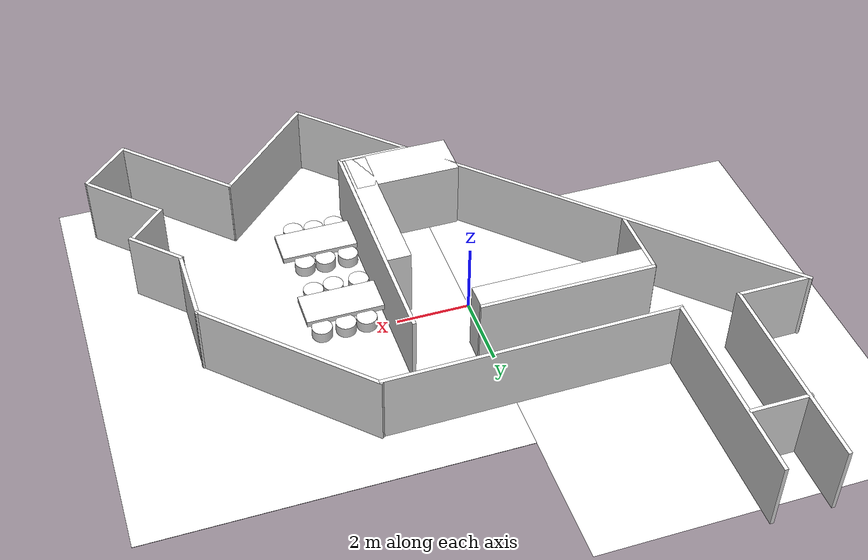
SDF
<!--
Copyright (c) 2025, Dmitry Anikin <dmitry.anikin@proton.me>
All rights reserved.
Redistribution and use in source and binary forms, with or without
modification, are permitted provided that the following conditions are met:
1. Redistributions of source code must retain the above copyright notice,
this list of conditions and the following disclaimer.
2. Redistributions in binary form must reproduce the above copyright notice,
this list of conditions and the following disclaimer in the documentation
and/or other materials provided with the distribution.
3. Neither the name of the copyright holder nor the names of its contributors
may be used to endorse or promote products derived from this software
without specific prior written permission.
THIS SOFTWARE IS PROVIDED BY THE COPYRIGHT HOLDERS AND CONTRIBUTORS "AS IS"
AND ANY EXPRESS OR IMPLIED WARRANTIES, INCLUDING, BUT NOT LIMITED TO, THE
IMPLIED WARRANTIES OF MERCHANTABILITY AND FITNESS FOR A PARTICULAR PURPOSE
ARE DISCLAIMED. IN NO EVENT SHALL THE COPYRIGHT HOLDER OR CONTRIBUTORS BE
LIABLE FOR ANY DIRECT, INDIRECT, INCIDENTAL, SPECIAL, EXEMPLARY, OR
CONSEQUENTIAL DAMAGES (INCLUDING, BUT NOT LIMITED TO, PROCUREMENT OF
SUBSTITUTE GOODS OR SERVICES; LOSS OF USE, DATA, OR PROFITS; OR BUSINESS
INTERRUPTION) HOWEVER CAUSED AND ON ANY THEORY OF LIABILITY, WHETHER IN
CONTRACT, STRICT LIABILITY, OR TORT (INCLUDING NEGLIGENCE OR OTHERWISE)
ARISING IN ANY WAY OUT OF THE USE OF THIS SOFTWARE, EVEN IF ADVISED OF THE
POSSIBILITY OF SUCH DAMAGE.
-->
<?xml version='1.0' encoding='ASCII'?>
<sdf version='1.7'>
  <world name='autonav_room'>
    <physics type="ode">
      <max_step_size>0.003</max_step_size>
      <real_time_factor>1.0</real_time_factor>
    </physics>
    <plugin name='ignition::gazebo::systems::Physics' filename='libignition-gazebo-physics-system.so'/>
    <plugin name='ignition::gazebo::systems::UserCommands' filename='libignition-gazebo-user-commands-system.so'/>
    <plugin name='ignition::gazebo::systems::SceneBroadcaster' filename='libignition-gazebo-scene-broadcaster-system.so'/>
    <plugin name="ignition::gazebo::systems::Sensors" filename="libignition-gazebo-sensors-system.so">
      <render_engine>ogre2</render_engine>
    </plugin>
    <plugin name="ignition::gazebo::systems::Imu" filename="libignition-gazebo-imu-system.so"/>
    <plugin name="ignition::gazebo::systems::NavSat" filename="libignition-gazebo-navsat-system.so"/>

    <scene>
      <ambient>1 1 1 1</ambient>
      <background>0.3 0.7 0.9 1</background>
      <shadows>0</shadows>
      <grid>false</grid>
    </scene>

    <spherical_coordinates>
      <surface_model>EARTH_WGS84</surface_model>
      <world_frame_orientation>ENU</world_frame_orientation>
      <latitude_deg>-22.986687</latitude_deg>
      <longitude_deg>-43.202501</longitude_deg>
      <elevation>0</elevation>
      <heading_deg>0</heading_deg>
    </spherical_coordinates>

    <light name='directionallight' type='directional'>
      <pose>-0.11616 -1.32396 2 0 -0 0</pose>
      <cast_shadows>false</cast_shadows>
      <intensity>1</intensity>
      <direction>0 0 -1</direction>
      <diffuse>0.8 0.8 0.8 1</diffuse>
      <specular>0.2 0.2 0.2 1</specular>
      <attenuation>
        <range>1000</range>
        <linear>0.01</linear>
        <constant>0.90000000000000002</constant>
        <quadratic>0.001</quadratic>
      </attenuation>
      <spot>
        <inner_angle>0</inner_angle>
        <outer_angle>0</outer_angle>
        <falloff>0</falloff>
      </spot>
    </light>

    <include>
      <uri>
        model://room
      </uri>
      <pose> 0 0 1 0 0 0</pose>
    </include>

    <include>
      <uri>
        model://floor
      </uri>
      <pose> -5 2.5 0 0 0 0</pose>
    </include>

    <include>
      <uri>
        model://floor
      </uri>
      <pose> 5 -1 0 0 0 0</pose>
      <name>floor_1</name>
    </include>

  </world>
</sdf>

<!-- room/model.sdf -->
<sdf version='1.7'>
 <model name='room'>
      <model name='room'>
        <model name='room'>
          <link name='Wall_0'>
            <pose>-1.90776 1.96744 0 0 -0 0</pose>
            <self_collide>0</self_collide>
            <enable_wind>0</enable_wind>
            <kinematic>0</kinematic>
            <inertial>
              <inertia>
                <ixx>0</ixx>
                <ixy>0</ixy>
                <ixz>0</ixz>
                <iyy>0</iyy>
                <iyz>0</iyz>
                <izz>0</izz>
              </inertia>
              <mass>0</mass>
              <pose>0 0 0 0 -0 0</pose>
            </inertial>
            <visual name='Wall_0_visual'>
              <geometry>
                <box>
                  <size>4.78884 0.1 2</size>
                </box>
              </geometry>
              <material>
                    <diffuse>1.0 1.0 1.0</diffuse>
                    <specular>1.0 1.0 1.0</specular>
                    <pbr>
                        <metal>
                            <albedo_map>materials/textures/2.jpg</albedo_map>
                            <normal_map>materials/textures/2.jpg</normal_map>
                        </metal>
                    </pbr>
                </material>
              <pose>0 0 0 0 -0 0</pose>
              <transparency>0</transparency>
              <cast_shadows>1</cast_shadows>
            </visual>
            <collision name='Wall_0_collision'>
              <laser_retro>0</laser_retro>
              <max_contacts>10</max_contacts>
              <pose>0 0 0 0 -0 0</pose>
              <geometry>
                <box>
                  <size>4.78884 0.1 2</size>
                </box>
              </geometry>
              <surface>
                <friction>
                  <ode>
                    <mu>1</mu>
                    <mu2>1</mu2>
                    <fdir1>0 0 0</fdir1>
                    <slip1>0</slip1>
                    <slip2>0</slip2>
                  </ode>
                  <torsional>
                    <coefficient>1</coefficient>
                    <patch_radius>0</patch_radius>
                    <surface_radius>0</surface_radius>
                    <use_patch_radius>1</use_patch_radius>
                    <ode>
                      <slip>0</slip>
                    </ode>
                  </torsional>
                </friction>
                <bounce>
                  <restitution_coefficient>0</restitution_coefficient>
                  <threshold>1e+06</threshold>
                </bounce>
                <contact>
                  <collide_without_contact>0</collide_without_contact>
                  <collide_without_contact_bitmask>1</collide_without_contact_bitmask>
                  <collide_bitmask>1</collide_bitmask>
                  <ode>
                    <soft_cfm>0</soft_cfm>
                    <soft_erp>0.2</soft_erp>
                    <kp>1e+13</kp>
                    <kd>1</kd>
                    <max_vel>0.01</max_vel>
                    <min_depth>0</min_depth>
                  </ode>
                  <bullet>
                    <split_impulse>1</split_impulse>
                    <split_impulse_penetration_threshold>-0.01</split_impulse_penetration_threshold>
                    <soft_cfm>0</soft_cfm>
                    <soft_erp>0.2</soft_erp>
                    <kp>1e+13</kp>
                    <kd>1</kd>
                  </bullet>
                </contact>
              </surface>
            </collision>
          </link>

          <link name='Wall_128'>
            <pose>7.26267 -1.04011 0 0 -0 1.5708</pose>
            <self_collide>0</self_collide>
            <enable_wind>0</enable_wind>
            <kinematic>0</kinematic>
            <inertial>
              <inertia>
                <ixx>0</ixx>
                <ixy>0</ixy>
                <ixz>0</ixz>
                <iyy>0</iyy>
                <iyz>0</iyz>
                <izz>0</izz>
              </inertia>
              <mass>0</mass>
              <pose>0 0 0 0 -0 0</pose>
            </inertial>
            <visual name='Wall_128_visual'>
              <geometry>
                <box>
                  <size>2.1419 0.1 2</size>
                </box>
              </geometry>
              <material>
                    <diffuse>1.0 1.0 1.0</diffuse>
                    <specular>1.0 1.0 1.0</specular>
                    <pbr>
                        <metal>
                            <albedo_map>materials/textures/2.jpg</albedo_map>
                            <normal_map>materials/textures/2.jpg</normal_map>
                        </metal>
                    </pbr>
                </material>
              <pose>0 0 0 0 -0 0</pose>
              <transparency>0</transparency>
              <cast_shadows>1</cast_shadows>
            </visual>
            <collision name='Wall_128_collision'>
              <laser_retro>0</laser_retro>
              <max_contacts>10</max_contacts>
              <pose>0 0 0 0 -0 0</pose>
              <geometry>
                <box>
                  <size>2.1419 0.1 2</size>
                </box>
              </geometry>
              <surface>
                <friction>
                  <ode>
                    <mu>1</mu>
                    <mu2>1</mu2>
                    <fdir1>0 0 0</fdir1>
                    <slip1>0</slip1>
                    <slip2>0</slip2>
                  </ode>
                  <torsional>
                    <coefficient>1</coefficient>
                    <patch_radius>0</patch_radius>
                    <surface_radius>0</surface_radius>
                    <use_patch_radius>1</use_patch_radius>
                    <ode>
                      <slip>0</slip>
                    </ode>
                  </torsional>
                </friction>
                <bounce>
                  <restitution_coefficient>0</restitution_coefficient>
                  <threshold>1e+06</threshold>
                </bounce>
                <contact>
                  <collide_without_contact>0</collide_without_contact>
                  <collide_without_contact_bitmask>1</collide_without_contact_bitmask>
                  <collide_bitmask>1</collide_bitmask>
                  <ode>
                    <soft_cfm>0</soft_cfm>
                    <soft_erp>0.2</soft_erp>
                    <kp>1e+13</kp>
                    <kd>1</kd>
                    <max_vel>0.01</max_vel>
                    <min_depth>0</min_depth>
                  </ode>
                  <bullet>
                    <split_impulse>1</split_impulse>
                    <split_impulse_penetration_threshold>-0.01</split_impulse_penetration_threshold>
                    <soft_cfm>0</soft_cfm>
                    <soft_erp>0.2</soft_erp>
                    <kp>1e+13</kp>
                    <kd>1</kd>
                  </bullet>
                </contact>
              </surface>
            </collision>
          </link>
          <link name='Wall_130'>
            <pose>7.80321 -2.68186 0 0 0 -0.785398</pose>
            <self_collide>0</self_collide>
            <enable_wind>0</enable_wind>
            <kinematic>0</kinematic>
            <inertial>
              <inertia>
                <ixx>0</ixx>
                <ixy>0</ixy>
                <ixz>0</ixz>
                <iyy>0</iyy>
                <iyz>0</iyz>
                <izz>0</izz>
              </inertia>
              <mass>0</mass>
              <pose>0 0 0 0 -0 0</pose>
            </inertial>
            <visual name='Wall_130_visual'>
              <geometry>
                <box>
                  <size>1.673 0.1 2</size>
                </box>
              </geometry>
              <material>
                    <diffuse>1.0 1.0 1.0</diffuse>
                    <specular>1.0 1.0 1.0</specular>
                    <pbr>
                        <metal>
                            <albedo_map>materials/textures/2.jpg</albedo_map>
                            <normal_map>materials/textures/2.jpg</normal_map>
                        </metal>
                    </pbr>
                </material>
              <pose>0 0 0 0 -0 0</pose>
              <transparency>0</transparency>
              <cast_shadows>1</cast_shadows>
            </visual>
            <collision name='Wall_130_collision'>
              <laser_retro>0</laser_retro>
              <max_contacts>10</max_contacts>
              <pose>0 0 0 0 -0 0</pose>
              <geometry>
                <box>
                  <size>1.673 0.1 2</size>
                </box>
              </geometry>
              <surface>
                <friction>
                  <ode>
                    <mu>1</mu>
                    <mu2>1</mu2>
                    <fdir1>0 0 0</fdir1>
                    <slip1>0</slip1>
                    <slip2>0</slip2>
                  </ode>
                  <torsional>
                    <coefficient>1</coefficient>
                    <patch_radius>0</patch_radius>
                    <surface_radius>0</surface_radius>
                    <use_patch_radius>1</use_patch_radius>
                    <ode>
                      <slip>0</slip>
                    </ode>
                  </torsional>
                </friction>
                <bounce>
                  <restitution_coefficient>0</restitution_coefficient>
                  <threshold>1e+06</threshold>
                </bounce>
                <contact>
                  <collide_without_contact>0</collide_without_contact>
                  <collide_without_contact_bitmask>1</collide_without_contact_bitmask>
                  <collide_bitmask>1</collide_bitmask>
                  <ode>
                    <soft_cfm>0</soft_cfm>
                    <soft_erp>0.2</soft_erp>
                    <kp>1e+13</kp>
                    <kd>1</kd>
                    <max_vel>0.01</max_vel>
                    <min_depth>0</min_depth>
                  </ode>
                  <bullet>
                    <split_impulse>1</split_impulse>
                    <split_impulse_penetration_threshold>-0.01</split_impulse_penetration_threshold>
                    <soft_cfm>0</soft_cfm>
                    <soft_erp>0.2</soft_erp>
                    <kp>1e+13</kp>
                    <kd>1</kd>
                  </bullet>
                </contact>
              </surface>
            </collision>
          </link>
          <link name='Wall_131'>
            <pose>7.85675 -3.68948 0 0 0 -2.35619</pose>
            <self_collide>0</self_collide>
            <enable_wind>0</enable_wind>
            <kinematic>0</kinematic>
            <inertial>
              <inertia>
                <ixx>0</ixx>
                <ixy>0</ixy>
                <ixz>0</ixz>
                <iyy>0</iyy>
                <iyz>0</iyz>
                <izz>0</izz>
              </inertia>
              <mass>0</mass>
              <pose>0 0 0 0 -0 0</pose>
            </inertial>
            <visual name='Wall_131_visual'>
              <geometry>
                <box>
                  <size>1.34958 0.1 2</size>
                </box>
              </geometry>
              <material>
                    <diffuse>1.0 1.0 1.0</diffuse>
                    <specular>1.0 1.0 1.0</specular>
                    <pbr>
                        <metal>
                            <albedo_map>materials/textures/2.jpg</albedo_map>
                            <normal_map>materials/textures/2.jpg</normal_map>
                        </metal>
                    </pbr>
                </material>
              <pose>0 0 0 0 -0 0</pose>
              <transparency>0</transparency>
              <cast_shadows>1</cast_shadows>
            </visual>
            <collision name='Wall_131_collision'>
              <laser_retro>0</laser_retro>
              <max_contacts>10</max_contacts>
              <pose>0 0 0 0 -0 0</pose>
              <geometry>
                <box>
                  <size>1.34958 0.1 2</size>
                </box>
              </geometry>
              <surface>
                <friction>
                  <ode>
                    <mu>1</mu>
                    <mu2>1</mu2>
                    <fdir1>0 0 0</fdir1>
                    <slip1>0</slip1>
                    <slip2>0</slip2>
                  </ode>
                  <torsional>
                    <coefficient>1</coefficient>
                    <patch_radius>0</patch_radius>
                    <surface_radius>0</surface_radius>
                    <use_patch_radius>1</use_patch_radius>
                    <ode>
                      <slip>0</slip>
                    </ode>
                  </torsional>
                </friction>
                <bounce>
                  <restitution_coefficient>0</restitution_coefficient>
                  <threshold>1e+06</threshold>
                </bounce>
                <contact>
                  <collide_without_contact>0</collide_without_contact>
                  <collide_without_contact_bitmask>1</collide_without_contact_bitmask>
                  <collide_bitmask>1</collide_bitmask>
                  <ode>
                    <soft_cfm>0</soft_cfm>
                    <soft_erp>0.2</soft_erp>
                    <kp>1e+13</kp>
                    <kd>1</kd>
                    <max_vel>0.01</max_vel>
                    <min_depth>0</min_depth>
                  </ode>
                  <bullet>
                    <split_impulse>1</split_impulse>
                    <split_impulse_penetration_threshold>-0.01</split_impulse_penetration_threshold>
                    <soft_cfm>0</soft_cfm>
                    <soft_erp>0.2</soft_erp>
                    <kp>1e+13</kp>
                    <kd>1</kd>
                  </bullet>
                </contact>
              </surface>
            </collision>
          </link>
          <link name='Wall_131_clone'>
            <pose>8.51574 -6.44612 0 0 0 -2.35619</pose>
            <self_collide>0</self_collide>
            <enable_wind>0</enable_wind>
            <kinematic>0</kinematic>
            <inertial>
              <inertia>
                <ixx>0</ixx>
                <ixy>0</ixy>
                <ixz>0</ixz>
                <iyy>0</iyy>
                <iyz>0</iyz>
                <izz>0</izz>
              </inertia>
              <mass>0</mass>
              <pose>0 0 0 0 -0 0</pose>
            </inertial>
            <visual name='Wall_131_visual'>
              <geometry>
                <box>
                  <size>1.75148 0.1 2</size>
                </box>
              </geometry>
              <material>
                    <diffuse>1.0 1.0 1.0</diffuse>
                    <specular>1.0 1.0 1.0</specular>
                    <pbr>
                        <metal>
                            <albedo_map>materials/textures/2.jpg</albedo_map>
                            <normal_map>materials/textures/2.jpg</normal_map>
                        </metal>
                    </pbr>
                </material>
              <pose>0 0 0 0 -0 0</pose>
              <transparency>0</transparency>
              <cast_shadows>1</cast_shadows>
            </visual>
            <collision name='Wall_131_collision'>
              <laser_retro>0</laser_retro>
              <max_contacts>10</max_contacts>
              <pose>0 0 0 0 -0 0</pose>
              <geometry>
                <box>
                  <size>1.75148 0.1 2</size>
                </box>
              </geometry>
              <surface>
                <friction>
                  <ode>
                    <mu>1</mu>
                    <mu2>1</mu2>
                    <fdir1>0 0 0</fdir1>
                    <slip1>0</slip1>
                    <slip2>0</slip2>
                  </ode>
                  <torsional>
                    <coefficient>1</coefficient>
                    <patch_radius>0</patch_radius>
                    <surface_radius>0</surface_radius>
                    <use_patch_radius>1</use_patch_radius>
                    <ode>
                      <slip>0</slip>
                    </ode>
                  </torsional>
                </friction>
                <bounce>
                  <restitution_coefficient>0</restitution_coefficient>
                  <threshold>1e+06</threshold>
                </bounce>
                <contact>
                  <collide_without_contact>0</collide_without_contact>
                  <collide_without_contact_bitmask>1</collide_without_contact_bitmask>
                  <collide_bitmask>1</collide_bitmask>
                  <ode>
                    <soft_cfm>0</soft_cfm>
                    <soft_erp>0.2</soft_erp>
                    <kp>1e+13</kp>
                    <kd>1</kd>
                    <max_vel>0.01</max_vel>
                    <min_depth>0</min_depth>
                  </ode>
                  <bullet>
                    <split_impulse>1</split_impulse>
                    <split_impulse_penetration_threshold>-0.01</split_impulse_penetration_threshold>
                    <soft_cfm>0</soft_cfm>
                    <soft_erp>0.2</soft_erp>
                    <kp>1e+13</kp>
                    <kd>1</kd>
                  </bullet>
                </contact>
              </surface>
            </collision>
          </link>
          <link name='Wall_133'>
            <pose>8.24461 -4.96449 0 0 0 -0.785398</pose>
            <self_collide>0</self_collide>
            <enable_wind>0</enable_wind>
            <kinematic>0</kinematic>
            <inertial>
              <inertia>
                <ixx>0</ixx>
                <ixy>0</ixy>
                <ixz>0</ixz>
                <iyy>0</iyy>
                <iyz>0</iyz>
                <izz>0</izz>
              </inertia>
              <mass>0</mass>
              <pose>0 0 0 0 -0 0</pose>
            </inertial>
            <visual name='Wall_133_visual'>
              <geometry>
                <box>
                  <size>2.4417 0.1 2</size>
                </box>
              </geometry>
              <material>
                    <diffuse>1.0 1.0 1.0</diffuse>
                    <specular>1.0 1.0 1.0</specular>
                    <pbr>
                        <metal>
                            <albedo_map>materials/textures/2.jpg</albedo_map>
                            <normal_map>materials/textures/2.jpg</normal_map>
                        </metal>
                    </pbr>
                </material>
              <pose>0 0 0 0 -0 0</pose>
              <transparency>0</transparency>
              <cast_shadows>1</cast_shadows>
            </visual>
            <collision name='Wall_133_collision'>
              <laser_retro>0</laser_retro>
              <max_contacts>10</max_contacts>
              <pose>0 0 0 0 -0 0</pose>
              <geometry>
                <box>
                  <size>2.4417 0.1 2</size>
                </box>
              </geometry>
              <surface>
                <friction>
                  <ode>
                    <mu>1</mu>
                    <mu2>1</mu2>
                    <fdir1>0 0 0</fdir1>
                    <slip1>0</slip1>
                    <slip2>0</slip2>
                  </ode>
                  <torsional>
                    <coefficient>1</coefficient>
                    <patch_radius>0</patch_radius>
                    <surface_radius>0</surface_radius>
                    <use_patch_radius>1</use_patch_radius>
                    <ode>
                      <slip>0</slip>
                    </ode>
                  </torsional>
                </friction>
                <bounce>
                  <restitution_coefficient>0</restitution_coefficient>
                  <threshold>1e+06</threshold>
                </bounce>
                <contact>
                  <collide_without_contact>0</collide_without_contact>
                  <collide_without_contact_bitmask>1</collide_without_contact_bitmask>
                  <collide_bitmask>1</collide_bitmask>
                  <ode>
                    <soft_cfm>0</soft_cfm>
                    <soft_erp>0.2</soft_erp>
                    <kp>1e+13</kp>
                    <kd>1</kd>
                    <max_vel>0.01</max_vel>
                    <min_depth>0</min_depth>
                  </ode>
                  <bullet>
                    <split_impulse>1</split_impulse>
                    <split_impulse_penetration_threshold>-0.01</split_impulse_penetration_threshold>
                    <soft_cfm>0</soft_cfm>
                    <soft_erp>0.2</soft_erp>
                    <kp>1e+13</kp>
                    <kd>1</kd>
                  </bullet>
                </contact>
              </surface>
            </collision>
          </link>
          <link name='Wall_136'>
            <pose>5.42768 1.79442 0 0 -0 2.35619</pose>
            <self_collide>0</self_collide>
            <enable_wind>0</enable_wind>
            <kinematic>0</kinematic>
            <inertial>
              <inertia>
                <ixx>0</ixx>
                <ixy>0</ixy>
                <ixz>0</ixz>
                <iyy>0</iyy>
                <iyz>0</iyz>
                <izz>0</izz>
              </inertia>
              <mass>0</mass>
              <pose>0 0 0 0 -0 0</pose>
            </inertial>
            <visual name='Wall_136_visual'>
              <geometry>
                <box>
                  <size>5.28176 0.1 2</size>
                </box>
              </geometry>
              <material>
                    <diffuse>1.0 1.0 1.0</diffuse>
                    <specular>1.0 1.0 1.0</specular>
                    <pbr>
                        <metal>
                            <albedo_map>materials/textures/2.jpg</albedo_map>
                            <normal_map>materials/textures/2.jpg</normal_map>
                        </metal>
                    </pbr>
                </material>
              <pose>0 0 0 0 -0 0</pose>
              <transparency>0</transparency>
              <cast_shadows>1</cast_shadows>
            </visual>
            <collision name='Wall_136_collision'>
              <laser_retro>0</laser_retro>
              <max_contacts>10</max_contacts>
              <pose>0 0 0 0 -0 0</pose>
              <geometry>
                <box>
                  <size>5.28176 0.1 2</size>
                </box>
              </geometry>
              <surface>
                <friction>
                  <ode>
                    <mu>1</mu>
                    <mu2>1</mu2>
                    <fdir1>0 0 0</fdir1>
                    <slip1>0</slip1>
                    <slip2>0</slip2>
                  </ode>
                  <torsional>
                    <coefficient>1</coefficient>
                    <patch_radius>0</patch_radius>
                    <surface_radius>0</surface_radius>
                    <use_patch_radius>1</use_patch_radius>
                    <ode>
                      <slip>0</slip>
                    </ode>
                  </torsional>
                </friction>
                <bounce>
                  <restitution_coefficient>0</restitution_coefficient>
                  <threshold>1e+06</threshold>
                </bounce>
                <contact>
                  <collide_without_contact>0</collide_without_contact>
                  <collide_without_contact_bitmask>1</collide_without_contact_bitmask>
                  <collide_bitmask>1</collide_bitmask>
                  <ode>
                    <soft_cfm>0</soft_cfm>
                    <soft_erp>0.2</soft_erp>
                    <kp>1e+13</kp>
                    <kd>1</kd>
                    <max_vel>0.01</max_vel>
                    <min_depth>0</min_depth>
                  </ode>
                  <bullet>
                    <split_impulse>1</split_impulse>
                    <split_impulse_penetration_threshold>-0.01</split_impulse_penetration_threshold>
                    <soft_cfm>0</soft_cfm>
                    <soft_erp>0.2</soft_erp>
                    <kp>1e+13</kp>
                    <kd>1</kd>
                  </bullet>
                </contact>
              </surface>
            </collision>
          </link>
          <link name='Wall_137'>
            <pose>-0.350288 3.5584 0 0 0 -3.13459</pose>
            <self_collide>0</self_collide>
            <enable_wind>0</enable_wind>
            <kinematic>0</kinematic>
            <inertial>
              <inertia>
                <ixx>0</ixx>
                <ixy>0</ixy>
                <ixz>0</ixz>
                <iyy>0</iyy>
                <iyz>0</iyz>
                <izz>0</izz>
              </inertia>
              <mass>0</mass>
              <pose>0 0 0 0 -0 0</pose>
            </inertial>
            <visual name='Wall_137_visual'>
              <geometry>
                <box>
                  <size>7.96727 0.1 2</size>
                </box>
              </geometry>
              <material>
                    <diffuse>1.0 1.0 1.0</diffuse>
                    <specular>1.0 1.0 1.0</specular>
                    <pbr>
                        <metal>
                            <albedo_map>materials/textures/2.jpg</albedo_map>
                            <normal_map>materials/textures/2.jpg</normal_map>
                        </metal>
                    </pbr>
                </material>
              <pose>0 0 0 0 -0 0</pose>
              <transparency>0</transparency>
              <cast_shadows>1</cast_shadows>
            </visual>
            <collision name='Wall_137_collision'>
              <laser_retro>0</laser_retro>
              <max_contacts>10</max_contacts>
              <pose>0 0 0 0 -0 0</pose>
              <geometry>
                <box>
                  <size>7.96727 0.1 2</size>
                </box>
              </geometry>
              <surface>
                <friction>
                  <ode>
                    <mu>1</mu>
                    <mu2>1</mu2>
                    <fdir1>0 0 0</fdir1>
                    <slip1>0</slip1>
                    <slip2>0</slip2>
                  </ode>
                  <torsional>
                    <coefficient>1</coefficient>
                    <patch_radius>0</patch_radius>
                    <surface_radius>0</surface_radius>
                    <use_patch_radius>1</use_patch_radius>
                    <ode>
                      <slip>0</slip>
                    </ode>
                  </torsional>
                </friction>
                <bounce>
                  <restitution_coefficient>0</restitution_coefficient>
                  <threshold>1e+06</threshold>
                </bounce>
                <contact>
                  <collide_without_contact>0</collide_without_contact>
                  <collide_without_contact_bitmask>1</collide_without_contact_bitmask>
                  <collide_bitmask>1</collide_bitmask>
                  <ode>
                    <soft_cfm>0</soft_cfm>
                    <soft_erp>0.2</soft_erp>
                    <kp>1e+13</kp>
                    <kd>1</kd>
                    <max_vel>0.01</max_vel>
                    <min_depth>0</min_depth>
                  </ode>
                  <bullet>
                    <split_impulse>1</split_impulse>
                    <split_impulse_penetration_threshold>-0.01</split_impulse_penetration_threshold>
                    <soft_cfm>0</soft_cfm>
                    <soft_erp>0.2</soft_erp>
                    <kp>1e+13</kp>
                    <kd>1</kd>
                  </bullet>
                </contact>
              </surface>
            </collision>
          </link>
          <link name='Wall_139'>
            <pose>-5.12619 7.12669 0 0 -0 0</pose>
            <self_collide>0</self_collide>
            <enable_wind>0</enable_wind>
            <kinematic>0</kinematic>
            <inertial>
              <inertia>
                <ixx>0</ixx>
                <ixy>0</ixy>
                <ixz>0</ixz>
                <iyy>0</iyy>
                <iyz>0</iyz>
                <izz>0</izz>
              </inertia>
              <mass>0</mass>
              <pose>0 0 0 0 -0 0</pose>
            </inertial>
            <visual name='Wall_139_visual'>
              <geometry>
                <box>
                  <size>1.66174 0.1 2</size>
                </box>
              </geometry>
              <material>
                    <diffuse>1.0 1.0 1.0</diffuse>
                    <specular>1.0 1.0 1.0</specular>
                    <pbr>
                        <metal>
                            <albedo_map>materials/textures/2.jpg</albedo_map>
                            <normal_map>materials/textures/2.jpg</normal_map>
                        </metal>
                    </pbr>
                </material>
              <pose>0 0 0 0 -0 0</pose>
              <transparency>0</transparency>
              <cast_shadows>1</cast_shadows>
            </visual>
            <collision name='Wall_139_collision'>
              <laser_retro>0</laser_retro>
              <max_contacts>10</max_contacts>
              <pose>0 0 0 0 -0 0</pose>
              <geometry>
                <box>
                  <size>1.66174 0.1 2</size>
                </box>
              </geometry>
              <surface>
                <friction>
                  <ode>
                    <mu>1</mu>
                    <mu2>1</mu2>
                    <fdir1>0 0 0</fdir1>
                    <slip1>0</slip1>
                    <slip2>0</slip2>
                  </ode>
                  <torsional>
                    <coefficient>1</coefficient>
                    <patch_radius>0</patch_radius>
                    <surface_radius>0</surface_radius>
                    <use_patch_radius>1</use_patch_radius>
                    <ode>
                      <slip>0</slip>
                    </ode>
                  </torsional>
                </friction>
                <bounce>
                  <restitution_coefficient>0</restitution_coefficient>
                  <threshold>1e+06</threshold>
                </bounce>
                <contact>
                  <collide_without_contact>0</collide_without_contact>
                  <collide_without_contact_bitmask>1</collide_without_contact_bitmask>
                  <collide_bitmask>1</collide_bitmask>
                  <ode>
                    <soft_cfm>0</soft_cfm>
                    <soft_erp>0.2</soft_erp>
                    <kp>1e+13</kp>
                    <kd>1</kd>
                    <max_vel>0.01</max_vel>
                    <min_depth>0</min_depth>
                  </ode>
                  <bullet>
                    <split_impulse>1</split_impulse>
                    <split_impulse_penetration_threshold>-0.01</split_impulse_penetration_threshold>
                    <soft_cfm>0</soft_cfm>
                    <soft_erp>0.2</soft_erp>
                    <kp>1e+13</kp>
                    <kd>1</kd>
                  </bullet>
                </contact>
              </surface>
            </collision>
          </link>
          <link name='Wall_20'>
            <pose>-4.27598 6.23196 0 0 -0 1.57077</pose>
            <self_collide>0</self_collide>
            <enable_wind>0</enable_wind>
            <kinematic>0</kinematic>
            <inertial>
              <inertia>
                <ixx>0</ixx>
                <ixy>0</ixy>
                <ixz>0</ixz>
                <iyy>0</iyy>
                <iyz>0</iyz>
                <izz>0</izz>
              </inertia>
              <mass>0</mass>
              <pose>0 0 0 0 -0 0</pose>
            </inertial>
            <visual name='Wall_20_visual'>
              <geometry>
                <box>
                  <size>5.3976 0.1 2</size>
                </box>
              </geometry>
              <material>
                    <diffuse>1.0 1.0 1.0</diffuse>
                    <specular>1.0 1.0 1.0</specular>
                    <pbr>
                        <metal>
                            <albedo_map>materials/textures/2.jpg</albedo_map>
                            <normal_map>materials/textures/2.jpg</normal_map>
                        </metal>
                    </pbr>
                </material>
              <pose>0 0 0 0 -0 0</pose>
              <transparency>0</transparency>
              <cast_shadows>1</cast_shadows>
            </visual>
            <collision name='Wall_20_collision'>
              <laser_retro>0</laser_retro>
              <max_contacts>10</max_contacts>
              <pose>0 0 0 0 -0 0</pose>
              <geometry>
                <box>
                  <size>5.3976 0.1 2</size>
                </box>
              </geometry>
              <surface>
                <friction>
                  <ode>
                    <mu>1</mu>
                    <mu2>1</mu2>
                    <fdir1>0 0 0</fdir1>
                    <slip1>0</slip1>
                    <slip2>0</slip2>
                  </ode>
                  <torsional>
                    <coefficient>1</coefficient>
                    <patch_radius>0</patch_radius>
                    <surface_radius>0</surface_radius>
                    <use_patch_radius>1</use_patch_radius>
                    <ode>
                      <slip>0</slip>
                    </ode>
                  </torsional>
                </friction>
                <bounce>
                  <restitution_coefficient>0</restitution_coefficient>
                  <threshold>1e+06</threshold>
                </bounce>
                <contact>
                  <collide_without_contact>0</collide_without_contact>
                  <collide_without_contact_bitmask>1</collide_without_contact_bitmask>
                  <collide_bitmask>1</collide_bitmask>
                  <ode>
                    <soft_cfm>0</soft_cfm>
                    <soft_erp>0.2</soft_erp>
                    <kp>1e+13</kp>
                    <kd>1</kd>
                    <max_vel>0.01</max_vel>
                    <min_depth>0</min_depth>
                  </ode>
                  <bullet>
                    <split_impulse>1</split_impulse>
                    <split_impulse_penetration_threshold>-0.01</split_impulse_penetration_threshold>
                    <soft_cfm>0</soft_cfm>
                    <soft_erp>0.2</soft_erp>
                    <kp>1e+13</kp>
                    <kd>1</kd>
                  </bullet>
                </contact>
              </surface>
            </collision>
          </link>
          <link name='Wall_26'>
            <pose>-5.87592 6.2355 0 0 -0 1.5708</pose>
            <self_collide>0</self_collide>
            <enable_wind>0</enable_wind>
            <kinematic>0</kinematic>
            <inertial>
              <inertia>
                <ixx>0</ixx>
                <ixy>0</ixy>
                <ixz>0</ixz>
                <iyy>0</iyy>
                <iyz>0</iyz>
                <izz>0</izz>
              </inertia>
              <mass>0</mass>
              <pose>0 0 0 0 -0 0</pose>
            </inertial>
            <visual name='Wall_26_visual'>
              <geometry>
                <box>
                  <size>5.46093 0.1 2</size>
                </box>
              </geometry>
              <material>
                    <diffuse>1.0 1.0 1.0</diffuse>
                    <specular>1.0 1.0 1.0</specular>
                    <pbr>
                        <metal>
                            <albedo_map>materials/textures/2.jpg</albedo_map>
                            <normal_map>materials/textures/2.jpg</normal_map>
                        </metal>
                    </pbr>
                </material>
              <pose>0 0 0 0 -0 0</pose>
              <transparency>0</transparency>
              <cast_shadows>1</cast_shadows>
            </visual>
            <collision name='Wall_26_collision'>
              <laser_retro>0</laser_retro>
              <max_contacts>10</max_contacts>
              <pose>0 0 0 0 -0 0</pose>
              <geometry>
                <box>
                  <size>5.46093 0.1 2</size>
                </box>
              </geometry>
              <surface>
                <friction>
                  <ode>
                    <mu>1</mu>
                    <mu2>1</mu2>
                    <fdir1>0 0 0</fdir1>
                    <slip1>0</slip1>
                    <slip2>0</slip2>
                  </ode>
                  <torsional>
                    <coefficient>1</coefficient>
                    <patch_radius>0</patch_radius>
                    <surface_radius>0</surface_radius>
                    <use_patch_radius>1</use_patch_radius>
                    <ode>
                      <slip>0</slip>
                    </ode>
                  </torsional>
                </friction>
                <bounce>
                  <restitution_coefficient>0</restitution_coefficient>
                  <threshold>1e+06</threshold>
                </bounce>
                <contact>
                  <collide_without_contact>0</collide_without_contact>
                  <collide_without_contact_bitmask>1</collide_without_contact_bitmask>
                  <collide_bitmask>1</collide_bitmask>
                  <ode>
                    <soft_cfm>0</soft_cfm>
                    <soft_erp>0.2</soft_erp>
                    <kp>1e+13</kp>
                    <kd>1</kd>
                    <max_vel>0.01</max_vel>
                    <min_depth>0</min_depth>
                  </ode>
                  <bullet>
                    <split_impulse>1</split_impulse>
                    <split_impulse_penetration_threshold>-0.01</split_impulse_penetration_threshold>
                    <soft_cfm>0</soft_cfm>
                    <soft_erp>0.2</soft_erp>
                    <kp>1e+13</kp>
                    <kd>1</kd>
                  </bullet>
                </contact>
              </surface>
            </collision>
          </link>
          <link name='Wall_32'>
            <pose>-6.86092 3.5605 0 0 -0 3.14159</pose>
            <self_collide>0</self_collide>
            <enable_wind>0</enable_wind>
            <kinematic>0</kinematic>
            <inertial>
              <inertia>
                <ixx>0</ixx>
                <ixy>0</ixy>
                <ixz>0</ixz>
                <iyy>0</iyy>
                <iyz>0</iyz>
                <izz>0</izz>
              </inertia>
              <mass>0</mass>
              <pose>0 0 0 0 -0 0</pose>
            </inertial>
            <visual name='Wall_32_visual'>
              <geometry>
                <box>
                  <size>2.02432 0.1 2</size>
                </box>
              </geometry>
              <material>
                    <diffuse>1.0 1.0 1.0</diffuse>
                    <specular>1.0 1.0 1.0</specular>
                    <pbr>
                        <metal>
                            <albedo_map>materials/textures/2.jpg</albedo_map>
                            <normal_map>materials/textures/2.jpg</normal_map>
                        </metal>
                    </pbr>
                </material>
              <pose>0 0 0 0 -0 0</pose>
              <transparency>0</transparency>
              <cast_shadows>1</cast_shadows>
            </visual>
            <collision name='Wall_32_collision'>
              <laser_retro>0</laser_retro>
              <max_contacts>10</max_contacts>
              <pose>0 0 0 0 -0 0</pose>
              <geometry>
                <box>
                  <size>2.02432 0.1 2</size>
                </box>
              </geometry>
              <surface>
                <friction>
                  <ode>
                    <mu>1</mu>
                    <mu2>1</mu2>
                    <fdir1>0 0 0</fdir1>
                    <slip1>0</slip1>
                    <slip2>0</slip2>
                  </ode>
                  <torsional>
                    <coefficient>1</coefficient>
                    <patch_radius>0</patch_radius>
                    <surface_radius>0</surface_radius>
                    <use_patch_radius>1</use_patch_radius>
                    <ode>
                      <slip>0</slip>
                    </ode>
                  </torsional>
                </friction>
                <bounce>
                  <restitution_coefficient>0</restitution_coefficient>
                  <threshold>1e+06</threshold>
                </bounce>
                <contact>
                  <collide_without_contact>0</collide_without_contact>
                  <collide_without_contact_bitmask>1</collide_without_contact_bitmask>
                  <collide_bitmask>1</collide_bitmask>
                  <ode>
                    <soft_cfm>0</soft_cfm>
                    <soft_erp>0.2</soft_erp>
                    <kp>1e+13</kp>
                    <kd>1</kd>
                    <max_vel>0.01</max_vel>
                    <min_depth>0</min_depth>
                  </ode>
                  <bullet>
                    <split_impulse>1</split_impulse>
                    <split_impulse_penetration_threshold>-0.01</split_impulse_penetration_threshold>
                    <soft_cfm>0</soft_cfm>
                    <soft_erp>0.2</soft_erp>
                    <kp>1e+13</kp>
                    <kd>1</kd>
                  </bullet>
                </contact>
              </surface>
            </collision>
          </link>
          <link name='Wall_34'>
            <pose>-2.51701 -1.76841 0 0 0 -0.785398</pose>
            <self_collide>0</self_collide>
            <enable_wind>0</enable_wind>
            <kinematic>0</kinematic>
            <inertial>
              <inertia>
                <ixx>0</ixx>
                <ixy>0</ixy>
                <ixz>0</ixz>
                <iyy>0</iyy>
                <iyz>0</iyz>
                <izz>0</izz>
              </inertia>
              <mass>0</mass>
              <pose>0 0 0 0 -0 0</pose>
            </inertial>
            <visual name='Wall_34_visual'>
              <geometry>
                <box>
                  <size>15.2746 0.1 2</size>
                </box>
              </geometry>
              <material>
                    <diffuse>1.0 1.0 1.0</diffuse>
                    <specular>1.0 1.0 1.0</specular>
                    <pbr>
                        <metal>
                            <albedo_map>materials/textures/2.jpg</albedo_map>
                            <normal_map>materials/textures/2.jpg</normal_map>
                        </metal>
                    </pbr>
                </material>
              <pose>0 0 0 0 -0 0</pose>
              <transparency>0</transparency>
              <cast_shadows>1</cast_shadows>
            </visual>
            <collision name='Wall_34_collision'>
              <laser_retro>0</laser_retro>
              <max_contacts>10</max_contacts>
              <pose>0 0 0 0 -0 0</pose>
              <geometry>
                <box>
                  <size>15.2746 0.1 2</size>
                </box>
              </geometry>
              <surface>
                <friction>
                  <ode>
                    <mu>1</mu>
                    <mu2>1</mu2>
                    <fdir1>0 0 0</fdir1>
                    <slip1>0</slip1>
                    <slip2>0</slip2>
                  </ode>
                  <torsional>
                    <coefficient>1</coefficient>
                    <patch_radius>0</patch_radius>
                    <surface_radius>0</surface_radius>
                    <use_patch_radius>1</use_patch_radius>
                    <ode>
                      <slip>0</slip>
                    </ode>
                  </torsional>
                </friction>
                <bounce>
                  <restitution_coefficient>0</restitution_coefficient>
                  <threshold>1e+06</threshold>
                </bounce>
                <contact>
                  <collide_without_contact>0</collide_without_contact>
                  <collide_without_contact_bitmask>1</collide_without_contact_bitmask>
                  <collide_bitmask>1</collide_bitmask>
                  <ode>
                    <soft_cfm>0</soft_cfm>
                    <soft_erp>0.2</soft_erp>
                    <kp>1e+13</kp>
                    <kd>1</kd>
                    <max_vel>0.01</max_vel>
                    <min_depth>0</min_depth>
                  </ode>
                  <bullet>
                    <split_impulse>1</split_impulse>
                    <split_impulse_penetration_threshold>-0.01</split_impulse_penetration_threshold>
                    <soft_cfm>0</soft_cfm>
                    <soft_erp>0.2</soft_erp>
                    <kp>1e+13</kp>
                    <kd>1</kd>
                  </bullet>
                </contact>
              </surface>
            </collision>
          </link>
          <link name='Wall_59'>
            <pose>1.28152 -4.64194 0 0 -0 0</pose>
            <self_collide>0</self_collide>
            <enable_wind>0</enable_wind>
            <kinematic>0</kinematic>
            <inertial>
              <inertia>
                <ixx>0</ixx>
                <ixy>0</ixy>
                <ixz>0</ixz>
                <iyy>0</iyy>
                <iyz>0</iyz>
                <izz>0</izz>
              </inertia>
              <mass>0</mass>
              <pose>0 0 0 0 -0 0</pose>
            </inertial>
            <visual name='Wall_59_visual'>
              <geometry>
                <box>
                  <size>1.93656 0.1 2</size>
                </box>
              </geometry>
              <material>
                    <diffuse>1.0 1.0 1.0</diffuse>
                    <specular>1.0 1.0 1.0</specular>
                    <pbr>
                        <metal>
                            <albedo_map>materials/textures/2.jpg</albedo_map>
                            <normal_map>materials/textures/2.jpg</normal_map>
                        </metal>
                    </pbr>
                </material>
              <pose>0 0 0 0 -0 0</pose>
              <transparency>0</transparency>
              <cast_shadows>1</cast_shadows>
            </visual>
            <collision name='Wall_59_collision'>
              <laser_retro>0</laser_retro>
              <max_contacts>10</max_contacts>
              <pose>0 0 0 0 -0 0</pose>
              <geometry>
                <box>
                  <size>1.93656 0.1 2</size>
                </box>
              </geometry>
              <surface>
                <friction>
                  <ode>
                    <mu>1</mu>
                    <mu2>1</mu2>
                    <fdir1>0 0 0</fdir1>
                    <slip1>0</slip1>
                    <slip2>0</slip2>
                  </ode>
                  <torsional>
                    <coefficient>1</coefficient>
                    <patch_radius>0</patch_radius>
                    <surface_radius>0</surface_radius>
                    <use_patch_radius>1</use_patch_radius>
                    <ode>
                      <slip>0</slip>
                    </ode>
                  </torsional>
                </friction>
                <bounce>
                  <restitution_coefficient>0</restitution_coefficient>
                  <threshold>1e+06</threshold>
                </bounce>
                <contact>
                  <collide_without_contact>0</collide_without_contact>
                  <collide_without_contact_bitmask>1</collide_without_contact_bitmask>
                  <collide_bitmask>1</collide_bitmask>
                  <ode>
                    <soft_cfm>0</soft_cfm>
                    <soft_erp>0.2</soft_erp>
                    <kp>1e+13</kp>
                    <kd>1</kd>
                    <max_vel>0.01</max_vel>
                    <min_depth>0</min_depth>
                  </ode>
                  <bullet>
                    <split_impulse>1</split_impulse>
                    <split_impulse_penetration_threshold>-0.01</split_impulse_penetration_threshold>
                    <soft_cfm>0</soft_cfm>
                    <soft_erp>0.2</soft_erp>
                    <kp>1e+13</kp>
                    <kd>1</kd>
                  </bullet>
                </contact>
              </surface>
            </collision>
          </link>
          <link name='Wall_6'>
            <pose>-4.27776 0.982444 0 0 0 -1.5708</pose>
            <self_collide>0</self_collide>
            <enable_wind>0</enable_wind>
            <kinematic>0</kinematic>
            <visual name='Wall_6_visual'>
              <geometry>
                <box>
                  <size>2 0.1 2</size>
                </box>
              </geometry>
              <material>
                    <diffuse>1.0 1.0 1.0</diffuse>
                    <specular>1.0 1.0 1.0</specular>
                    <pbr>
                        <metal>
                            <albedo_map>materials/textures/2.jpg</albedo_map>
                            <normal_map>materials/textures/2.jpg</normal_map>
                        </metal>
                    </pbr>
                </material>
              <pose>0 0 0 0 -0 0</pose>
              <transparency>0</transparency>
              <cast_shadows>1</cast_shadows>
            </visual>
            <collision name='Wall_6_collision'>
              <laser_retro>0</laser_retro>
              <max_contacts>10</max_contacts>
              <pose>0 0 0 0 -0 0</pose>
              <geometry>
                <box>
                  <size>2 0.1 2</size>
                </box>
              </geometry>
              <surface>
                <friction>
                  <ode>
                    <mu>1</mu>
                    <mu2>1</mu2>
                    <fdir1>0 0 0</fdir1>
                    <slip1>0</slip1>
                    <slip2>0</slip2>
                  </ode>
                  <torsional>
                    <coefficient>1</coefficient>
                    <patch_radius>0</patch_radius>
                    <surface_radius>0</surface_radius>
                    <use_patch_radius>1</use_patch_radius>
                    <ode>
                      <slip>0</slip>
                    </ode>
                  </torsional>
                </friction>
                <bounce>
                  <restitution_coefficient>0</restitution_coefficient>
                  <threshold>1e+06</threshold>
                </bounce>
                <contact>
                  <collide_without_contact>0</collide_without_contact>
                  <collide_without_contact_bitmask>1</collide_without_contact_bitmask>
                  <collide_bitmask>1</collide_bitmask>
                  <ode>
                    <soft_cfm>0</soft_cfm>
                    <soft_erp>0.2</soft_erp>
                    <kp>1e+13</kp>
                    <kd>1</kd>
                    <max_vel>0.01</max_vel>
                    <min_depth>0</min_depth>
                  </ode>
                  <bullet>
                    <split_impulse>1</split_impulse>
                    <split_impulse_penetration_threshold>-0.01</split_impulse_penetration_threshold>
                    <soft_cfm>0</soft_cfm>
                    <soft_erp>0.2</soft_erp>
                    <kp>1e+13</kp>
                    <kd>1</kd>
                  </bullet>
                </contact>
              </surface>
            </collision>
          </link>
          <link name='Wall_61'>
            <pose>2.25369 -1.32302 0 0 0 -1.5687</pose>
            <self_collide>0</self_collide>
            <enable_wind>0</enable_wind>
            <kinematic>0</kinematic>
            <inertial>
              <inertia>
                <ixx>0</ixx>
                <ixy>0</ixy>
                <ixz>0</ixz>
                <iyy>0</iyy>
                <iyz>0</iyz>
                <izz>0</izz>
              </inertia>
              <mass>0</mass>
              <pose>0 0 0 0 -0 0</pose>
            </inertial>
            <visual name='Wall_61_visual'>
              <geometry>
                <box>
                  <size>6.70464 0.1 2</size>
                </box>
              </geometry>
              <material>
                    <diffuse>1.0 1.0 1.0</diffuse>
                    <specular>1.0 1.0 1.0</specular>
                    <pbr>
                        <metal>
                            <albedo_map>materials/textures/2.jpg</albedo_map>
                            <normal_map>materials/textures/2.jpg</normal_map>
                        </metal>
                    </pbr>
                </material>
              <pose>0 0 0 0 -0 0</pose>
              <transparency>0</transparency>
              <cast_shadows>1</cast_shadows>
            </visual>
            <collision name='Wall_61_collision'>
              <laser_retro>0</laser_retro>
              <max_contacts>10</max_contacts>
              <pose>0 0 0 0 -0 0</pose>
              <geometry>
                <box>
                  <size>6.70464 0.1 2</size>
                </box>
              </geometry>
              <surface>
                <friction>
                  <ode>
                    <mu>1</mu>
                    <mu2>1</mu2>
                    <fdir1>0 0 0</fdir1>
                    <slip1>0</slip1>
                    <slip2>0</slip2>
                  </ode>
                  <torsional>
                    <coefficient>1</coefficient>
                    <patch_radius>0</patch_radius>
                    <surface_radius>0</surface_radius>
                    <use_patch_radius>1</use_patch_radius>
                    <ode>
                      <slip>0</slip>
                    </ode>
                  </torsional>
                </friction>
                <bounce>
                  <restitution_coefficient>0</restitution_coefficient>
                  <threshold>1e+06</threshold>
                </bounce>
                <contact>
                  <collide_without_contact>0</collide_without_contact>
                  <collide_without_contact_bitmask>1</collide_without_contact_bitmask>
                  <collide_bitmask>1</collide_bitmask>
                  <ode>
                    <soft_cfm>0</soft_cfm>
                    <soft_erp>0.2</soft_erp>
                    <kp>1e+13</kp>
                    <kd>1</kd>
                    <max_vel>0.01</max_vel>
                    <min_depth>0</min_depth>
                  </ode>
                  <bullet>
                    <split_impulse>1</split_impulse>
                    <split_impulse_penetration_threshold>-0.01</split_impulse_penetration_threshold>
                    <soft_cfm>0</soft_cfm>
                    <soft_erp>0.2</soft_erp>
                    <kp>1e+13</kp>
                    <kd>1</kd>
                  </bullet>
                </contact>
              </surface>
            </collision>
          </link>
          <link name='Wall_86'>
            <pose>4.13128 -5.82818 0 0 -0 0.785398</pose>
            <self_collide>0</self_collide>
            <enable_wind>0</enable_wind>
            <kinematic>0</kinematic>
            <inertial>
              <inertia>
                <ixx>0</ixx>
                <ixy>0</ixy>
                <ixz>0</ixz>
                <iyy>0</iyy>
                <iyz>0</iyz>
                <izz>0</izz>
              </inertia>
              <mass>0</mass>
              <pose>0 0 0 0 -0 0</pose>
            </inertial>
            <visual name='Wall_86_visual'>
              <geometry>
                <box>
                  <size>3.75782 0.1 2</size>
                </box>
              </geometry>
              <material>
                    <diffuse>1.0 1.0 1.0</diffuse>
                    <specular>1.0 1.0 1.0</specular>
                    <pbr>
                        <metal>
                            <albedo_map>materials/textures/2.jpg</albedo_map>
                            <normal_map>materials/textures/2.jpg</normal_map>
                        </metal>
                    </pbr>
                </material>
              <pose>0 0 0 0 -0 0</pose>
              <transparency>0</transparency>
              <cast_shadows>1</cast_shadows>
            </visual>
            <collision name='Wall_86_collision'>
              <laser_retro>0</laser_retro>
              <max_contacts>10</max_contacts>
              <pose>0 0 0 0 -0 0</pose>
              <geometry>
                <box>
                  <size>3.75782 0.1 2</size>
                </box>
              </geometry>
              <surface>
                <friction>
                  <ode>
                    <mu>1</mu>
                    <mu2>1</mu2>
                    <fdir1>0 0 0</fdir1>
                    <slip1>0</slip1>
                    <slip2>0</slip2>
                  </ode>
                  <torsional>
                    <coefficient>1</coefficient>
                    <patch_radius>0</patch_radius>
                    <surface_radius>0</surface_radius>
                    <use_patch_radius>1</use_patch_radius>
                    <ode>
                      <slip>0</slip>
                    </ode>
                  </torsional>
                </friction>
                <bounce>
                  <restitution_coefficient>0</restitution_coefficient>
                  <threshold>1e+06</threshold>
                </bounce>
                <contact>
                  <collide_without_contact>0</collide_without_contact>
                  <collide_without_contact_bitmask>1</collide_without_contact_bitmask>
                  <collide_bitmask>1</collide_bitmask>
                  <ode>
                    <soft_cfm>0</soft_cfm>
                    <soft_erp>0.2</soft_erp>
                    <kp>1e+13</kp>
                    <kd>1</kd>
                    <max_vel>0.01</max_vel>
                    <min_depth>0</min_depth>
                  </ode>
                  <bullet>
                    <split_impulse>1</split_impulse>
                    <split_impulse_penetration_threshold>-0.01</split_impulse_penetration_threshold>
                    <soft_cfm>0</soft_cfm>
                    <soft_erp>0.2</soft_erp>
                    <kp>1e+13</kp>
                    <kd>1</kd>
                  </bullet>
                </contact>
              </surface>
            </collision>
          </link>
          <link name='Wall_88'>
            <pose>6.67159 -5.77982 0 0 0 -0.785398</pose>
            <self_collide>0</self_collide>
            <enable_wind>0</enable_wind>
            <kinematic>0</kinematic>
            <inertial>
              <inertia>
                <ixx>0</ixx>
                <ixy>0</ixy>
                <ixz>0</ixz>
                <iyy>0</iyy>
                <iyz>0</iyz>
                <izz>0</izz>
              </inertia>
              <mass>0</mass>
              <pose>0 0 0 0 -0 0</pose>
            </inertial>
            <visual name='Wall_88_visual'>
              <geometry>
                <box>
                  <size>3.5417 0.1 2</size>
                </box>
              </geometry>
              <material>
                    <diffuse>1.0 1.0 1.0</diffuse>
                    <specular>1.0 1.0 1.0</specular>
                    <pbr>
                        <metal>
                            <albedo_map>materials/textures/2.jpg</albedo_map>
                            <normal_map>materials/textures/2.jpg</normal_map>
                        </metal>
                    </pbr>
                </material>
              <pose>0 0 0 0 -0 0</pose>
              <transparency>0</transparency>
              <cast_shadows>1</cast_shadows>
            </visual>
            <collision name='Wall_88_collision'>
              <laser_retro>0</laser_retro>
              <max_contacts>10</max_contacts>
              <pose>0 0 0 0 -0 0</pose>
              <geometry>
                <box>
                  <size>3.5417 0.1 2</size>
                </box>
              </geometry>
              <surface>
                <friction>
                  <ode>
                    <mu>1</mu>
                    <mu2>1</mu2>
                    <fdir1>0 0 0</fdir1>
                    <slip1>0</slip1>
                    <slip2>0</slip2>
                  </ode>
                  <torsional>
                    <coefficient>1</coefficient>
                    <patch_radius>0</patch_radius>
                    <surface_radius>0</surface_radius>
                    <use_patch_radius>1</use_patch_radius>
                    <ode>
                      <slip>0</slip>
                    </ode>
                  </torsional>
                </friction>
                <bounce>
                  <restitution_coefficient>0</restitution_coefficient>
                  <threshold>1e+06</threshold>
                </bounce>
                <contact>
                  <collide_without_contact>0</collide_without_contact>
                  <collide_without_contact_bitmask>1</collide_without_contact_bitmask>
                  <collide_bitmask>1</collide_bitmask>
                  <ode>
                    <soft_cfm>0</soft_cfm>
                    <soft_erp>0.2</soft_erp>
                    <kp>1e+13</kp>
                    <kd>1</kd>
                    <max_vel>0.01</max_vel>
                    <min_depth>0</min_depth>
                  </ode>
                  <bullet>
                    <split_impulse>1</split_impulse>
                    <split_impulse_penetration_threshold>-0.01</split_impulse_penetration_threshold>
                    <soft_cfm>0</soft_cfm>
                    <soft_erp>0.2</soft_erp>
                    <kp>1e+13</kp>
                    <kd>1</kd>
                  </bullet>
                </contact>
              </surface>
            </collision>
          </link>
          <link name='link_0_clone'>
            <inertial>
              <mass>0.352049</mass>
              <inertia>
                <ixx>0.0300666</ixx>
                <ixy>0</ixy>
                <ixz>0</ixz>
                <iyy>0.147153</iyy>
                <iyz>0</iyz>
                <izz>0.175761</izz>
              </inertia>
              <pose>0 0 0 0 -0 0</pose>
            </inertial>
            <pose>3.31097 -0.855745 -0.676988 0 -0 0</pose>
            <self_collide>0</self_collide>
            <enable_wind>0</enable_wind>
            <kinematic>0</kinematic>
            <visual name='visual'>
              <pose>0 0 0 0 -0 0</pose>
              <geometry>
                <box>
                  <size>2.23406 1 0.157656</size>
                </box>
              </geometry>
              <material>
                    <diffuse>1.0 1.0 1.0</diffuse>
                    <specular>1.0 1.0 1.0</specular>
                    <pbr>
                        <metal>
                            <albedo_map>materials/textures/5.jpg</albedo_map>
                            <normal_map>materials/textures/5.jpg</normal_map>
                        </metal>
                    </pbr>
                </material>
              <transparency>0</transparency>
              <cast_shadows>1</cast_shadows>
            </visual>
            <collision name='collision'>
              <laser_retro>0</laser_retro>
              <max_contacts>10</max_contacts>
              <pose>0 0 0 0 -0 0</pose>
              <geometry>
                <box>
                  <size>2.23406 1 0.157656</size>
                </box>
              </geometry>
              <surface>
                <friction>
                  <ode>
                    <mu>1</mu>
                    <mu2>1</mu2>
                    <fdir1>0 0 0</fdir1>
                    <slip1>0</slip1>
                    <slip2>0</slip2>
                  </ode>
                  <torsional>
                    <coefficient>1</coefficient>
                    <patch_radius>0</patch_radius>
                    <surface_radius>0</surface_radius>
                    <use_patch_radius>1</use_patch_radius>
                    <ode>
                      <slip>0</slip>
                    </ode>
                  </torsional>
                </friction>
                <bounce>
                  <restitution_coefficient>0</restitution_coefficient>
                  <threshold>1e+06</threshold>
                </bounce>
                <contact>
                  <collide_without_contact>0</collide_without_contact>
                  <collide_without_contact_bitmask>1</collide_without_contact_bitmask>
                  <collide_bitmask>1</collide_bitmask>
                  <ode>
                    <soft_cfm>0</soft_cfm>
                    <soft_erp>0.2</soft_erp>
                    <kp>1e+13</kp>
                    <kd>1</kd>
                    <max_vel>0.01</max_vel>
                    <min_depth>0</min_depth>
                  </ode>
                  <bullet>
                    <split_impulse>1</split_impulse>
                    <split_impulse_penetration_threshold>-0.01</split_impulse_penetration_threshold>
                    <soft_cfm>0</soft_cfm>
                    <soft_erp>0.2</soft_erp>
                    <kp>1e+13</kp>
                    <kd>1</kd>
                  </bullet>
                </contact>
              </surface>
            </collision>
          </link>
          <link name='link_0_clone_clone'>
            <inertial>
              <mass>0.507744</mass>
              <inertia>
                <ixx>0.0202588</ixx>
                <ixy>0</ixy>
                <ixz>0</ixz>
                <iyy>0.967968</iyy>
                <iyz>0</iyz>
                <izz>0.986123</izz>
              </inertia>
              <pose>0 0 0 0 -0 0</pose>
            </inertial>
            <pose>-1.91901 1.61007 0 0 -0 0</pose>
            <self_collide>0</self_collide>
            <enable_wind>0</enable_wind>
            <kinematic>0</kinematic>
            <visual name='visual'>
              <pose>0 0 0 0 -0 0</pose>
              <geometry>
                <box>
                  <size>4.78038 0.673751 2</size>
                </box>
              </geometry>
              <material>
                    <diffuse>1.0 1.0 1.0</diffuse>
                    <specular>1.0 1.0 1.0</specular>
                    <pbr>
                        <metal>
                            <albedo_map>materials/textures/2.jpg</albedo_map>
                            <normal_map>materials/textures/2.jpg</normal_map>
                        </metal>
                    </pbr>
                </material>
              <transparency>0</transparency>
              <cast_shadows>1</cast_shadows>
            </visual>
            <collision name='collision'>
              <laser_retro>0</laser_retro>
              <max_contacts>10</max_contacts>
              <pose>0 0 0 0 -0 0</pose>
              <geometry>
                <box>
                  <size>4.78038 0.673751 2</size>
                </box>
              </geometry>
              <surface>
                <friction>
                  <ode>
                    <mu>1</mu>
                    <mu2>1</mu2>
                    <fdir1>0 0 0</fdir1>
                    <slip1>0</slip1>
                    <slip2>0</slip2>
                  </ode>
                  <torsional>
                    <coefficient>1</coefficient>
                    <patch_radius>0</patch_radius>
                    <surface_radius>0</surface_radius>
                    <use_patch_radius>1</use_patch_radius>
                    <ode>
                      <slip>0</slip>
                    </ode>
                  </torsional>
                </friction>
                <bounce>
                  <restitution_coefficient>0</restitution_coefficient>
                  <threshold>1e+06</threshold>
                </bounce>
                <contact>
                  <collide_without_contact>0</collide_without_contact>
                  <collide_without_contact_bitmask>1</collide_without_contact_bitmask>
                  <collide_bitmask>1</collide_bitmask>
                  <ode>
                    <soft_cfm>0</soft_cfm>
                    <soft_erp>0.2</soft_erp>
                    <kp>1e+13</kp>
                    <kd>1</kd>
                    <max_vel>0.01</max_vel>
                    <min_depth>0</min_depth>
                  </ode>
                  <bullet>
                    <split_impulse>1</split_impulse>
                    <split_impulse_penetration_threshold>-0.01</split_impulse_penetration_threshold>
                    <soft_cfm>0</soft_cfm>
                    <soft_erp>0.2</soft_erp>
                    <kp>1e+13</kp>
                    <kd>1</kd>
                  </bullet>
                </contact>
              </surface>
            </collision>
          </link>
          <link name='link_0_clone_clone_0'>
            <inertial>
              <mass>0.346317</mass>
              <inertia>
                <ixx>0.0295771</ixx>
                <ixy>0</ixy>
                <ixz>0</ixz>
                <iyy>0.140056</iyy>
                <iyz>0</iyz>
                <izz>0.168198</izz>
              </inertia>
              <pose>0 0 0 0 -0 0</pose>
            </inertial>
            <pose>3.32202 -3.40677 -0.676988 0 -0 0</pose>
            <self_collide>0</self_collide>
            <enable_wind>0</enable_wind>
            <kinematic>0</kinematic>
            <visual name='visual'>
              <pose>0 0 0 0 -0 0</pose>
              <geometry>
                <box>
                  <size>2.1973 1 0.157656</size>
                </box>
              </geometry>
              <material>
                    <diffuse>1.0 1.0 1.0</diffuse>
                    <specular>1.0 1.0 1.0</specular>
                    <pbr>
                        <metal>
                            <albedo_map>materials/textures/5.jpg</albedo_map>
                            <normal_map>materials/textures/5.jpg</normal_map>
                        </metal>
                    </pbr>
                </material>
              <transparency>0</transparency>
              <cast_shadows>1</cast_shadows>
            </visual>
            <collision name='collision'>
              <laser_retro>0</laser_retro>
              <max_contacts>10</max_contacts>
              <pose>0 0 0 0 -0 0</pose>
              <geometry>
                <box>
                  <size>2.1973 1 0.157656</size>
                </box>
              </geometry>
              <surface>
                <friction>
                  <ode>
                    <mu>1</mu>
                    <mu2>1</mu2>
                    <fdir1>0 0 0</fdir1>
                    <slip1>0</slip1>
                    <slip2>0</slip2>
                  </ode>
                  <torsional>
                    <coefficient>1</coefficient>
                    <patch_radius>0</patch_radius>
                    <surface_radius>0</surface_radius>
                    <use_patch_radius>1</use_patch_radius>
                    <ode>
                      <slip>0</slip>
                    </ode>
                  </torsional>
                </friction>
                <bounce>
                  <restitution_coefficient>0</restitution_coefficient>
                  <threshold>1e+06</threshold>
                </bounce>
                <contact>
                  <collide_without_contact>0</collide_without_contact>
                  <collide_without_contact_bitmask>1</collide_without_contact_bitmask>
                  <collide_bitmask>1</collide_bitmask>
                  <ode>
                    <soft_cfm>0</soft_cfm>
                    <soft_erp>0.2</soft_erp>
                    <kp>1e+13</kp>
                    <kd>1</kd>
                    <max_vel>0.01</max_vel>
                    <min_depth>0</min_depth>
                  </ode>
                  <bullet>
                    <split_impulse>1</split_impulse>
                    <split_impulse_penetration_threshold>-0.01</split_impulse_penetration_threshold>
                    <soft_cfm>0</soft_cfm>
                    <soft_erp>0.2</soft_erp>
                    <kp>1e+13</kp>
                    <kd>1</kd>
                  </bullet>
                </contact>
              </surface>
            </collision>
          </link>
          <link name='link_0_clone_clone_clone'>
            <inertial>
              <mass>0.435868</mass>
              <inertia>
                <ixx>0.647791</ixx>
                <ixy>0</ixy>
                <ixz>0</ixz>
                <iyy>0.0164978</iyy>
                <iyz>0</iyz>
                <izz>0.662483</izz>
              </inertia>
              <pose>0 0 0 0 -0 0</pose>
            </inertial>
            <pose>1.87513 -2.46135 0 0 -0 0</pose>
            <self_collide>0</self_collide>
            <enable_wind>0</enable_wind>
            <kinematic>0</kinematic>
            <visual name='visual'>
              <pose>0 0 0 0 -0 0</pose>
              <geometry>
                <box>
                  <size>0.655248 4.22015 2</size>
                </box>
              </geometry>
              <material>
                    <diffuse>1.0 1.0 1.0</diffuse>
                    <specular>1.0 1.0 1.0</specular>
                    <pbr>
                        <metal>
                            <albedo_map>materials/textures/2.jpg</albedo_map>
                            <normal_map>materials/textures/2.jpg</normal_map>
                        </metal>
                    </pbr>
                </material>
              <transparency>0</transparency>
              <cast_shadows>1</cast_shadows>
            </visual>
            <collision name='collision'>
              <laser_retro>0</laser_retro>
              <max_contacts>10</max_contacts>
              <pose>0 0 0 0 -0 0</pose>
              <geometry>
                <box>
                  <size>0.655248 4.22015 2</size>
                </box>
              </geometry>
              <surface>
                <friction>
                  <ode>
                    <mu>1</mu>
                    <mu2>1</mu2>
                    <fdir1>0 0 0</fdir1>
                    <slip1>0</slip1>
                    <slip2>0</slip2>
                  </ode>
                  <torsional>
                    <coefficient>1</coefficient>
                    <patch_radius>0</patch_radius>
                    <surface_radius>0</surface_radius>
                    <use_patch_radius>1</use_patch_radius>
                    <ode>
                      <slip>0</slip>
                    </ode>
                  </torsional>
                </friction>
                <bounce>
                  <restitution_coefficient>0</restitution_coefficient>
                  <threshold>1e+06</threshold>
                </bounce>
                <contact>
                  <collide_without_contact>0</collide_without_contact>
                  <collide_without_contact_bitmask>1</collide_without_contact_bitmask>
                  <collide_bitmask>1</collide_bitmask>
                  <ode>
                    <soft_cfm>0</soft_cfm>
                    <soft_erp>0.2</soft_erp>
                    <kp>1e+13</kp>
                    <kd>1</kd>
                    <max_vel>0.01</max_vel>
                    <min_depth>0</min_depth>
                  </ode>
                  <bullet>
                    <split_impulse>1</split_impulse>
                    <split_impulse_penetration_threshold>-0.01</split_impulse_penetration_threshold>
                    <soft_cfm>0</soft_cfm>
                    <soft_erp>0.2</soft_erp>
                    <kp>1e+13</kp>
                    <kd>1</kd>
                  </bullet>
                </contact>
              </surface>
            </collision>
          </link>
          <link name='link_0_clone_clone_clone_clone'>
            <inertial>
              <mass>0.591923</mass>
              <inertia>
                <ixx>0.0827781</ixx>
                <ixy>0</ixy>
                <ixz>0</ixz>
                <iyy>0.421971</iyy>
                <iyz>0</iyz>
                <izz>0.502297</izz>
              </inertia>
              <pose>0 0 0 0 -0 0</pose>
            </inertial>
            <pose>0.665627 -3.98047 0 0 -0 0</pose>
            <self_collide>0</self_collide>
            <enable_wind>0</enable_wind>
            <kinematic>0</kinematic>
            <visual name='visual'>
              <pose>0 0 0 0 -0 0</pose>
              <geometry>
                <box>
                  <size>2.92057 1.28581 2</size>
                </box>
              </geometry>
              <material>
                    <diffuse>1.0 1.0 1.0</diffuse>
                    <specular>1.0 1.0 1.0</specular>
                    <pbr>
                        <metal>
                            <albedo_map>materials/textures/2.jpg</albedo_map>
                            <normal_map>materials/textures/2.jpg</normal_map>
                        </metal>
                    </pbr>
                </material>
              <transparency>0</transparency>
              <cast_shadows>1</cast_shadows>
            </visual>
            <collision name='collision'>
              <laser_retro>0</laser_retro>
              <max_contacts>10</max_contacts>
              <pose>0 0 0 0 -0 0</pose>
              <geometry>
                <box>
                  <size>2.92057 1.28581 2</size>
                </box>
              </geometry>
              <surface>
                <friction>
                  <ode>
                    <mu>1</mu>
                    <mu2>1</mu2>
                    <fdir1>0 0 0</fdir1>
                    <slip1>0</slip1>
                    <slip2>0</slip2>
                  </ode>
                  <torsional>
                    <coefficient>1</coefficient>
                    <patch_radius>0</patch_radius>
                    <surface_radius>0</surface_radius>
                    <use_patch_radius>1</use_patch_radius>
                    <ode>
                      <slip>0</slip>
                    </ode>
                  </torsional>
                </friction>
                <bounce>
                  <restitution_coefficient>0</restitution_coefficient>
                  <threshold>1e+06</threshold>
                </bounce>
                <contact>
                  <collide_without_contact>0</collide_without_contact>
                  <collide_without_contact_bitmask>1</collide_without_contact_bitmask>
                  <collide_bitmask>1</collide_bitmask>
                  <ode>
                    <soft_cfm>0</soft_cfm>
                    <soft_erp>0.2</soft_erp>
                    <kp>1e+13</kp>
                    <kd>1</kd>
                    <max_vel>0.01</max_vel>
                    <min_depth>0</min_depth>
                  </ode>
                  <bullet>
                    <split_impulse>1</split_impulse>
                    <split_impulse_penetration_threshold>-0.01</split_impulse_penetration_threshold>
                    <soft_cfm>0</soft_cfm>
                    <soft_erp>0.2</soft_erp>
                    <kp>1e+13</kp>
                    <kd>1</kd>
                  </bullet>
                </contact>
              </surface>
            </collision>
          </link>
          <link name='link_2_clone'>
            <inertial>
              <mass>0.00428311</mass>
              <inertia>
                <ixx>4.31093e-05</ixx>
                <ixy>0</ixy>
                <ixz>0</ixz>
                <iyy>4.31093e-05</iyy>
                <iyz>0</iyz>
                <izz>6.88364e-06</izz>
              </inertia>
              <pose>0 0 0 0 -0 0</pose>
            </inertial>
            <pose>4.06093 -3.69692 -0.833988 0 -0 0</pose>
            <self_collide>0</self_collide>
            <enable_wind>0</enable_wind>
            <kinematic>0</kinematic>
            <visual name='visual'>
              <pose>0 0 0 0 -0 0</pose>
              <geometry>
                <cylinder>
                  <radius>0.0566947</radius>
                  <length>0.333372</length>
                </cylinder>
              </geometry>
              <material>
                    <diffuse>1.0 1.0 1.0</diffuse>
                    <specular>1.0 1.0 1.0</specular>
                    <pbr>
                        <metal>
                            <albedo_map>materials/textures/5.jpg</albedo_map>
                            <normal_map>materials/textures/5.jpg</normal_map>
                        </metal>
                    </pbr>
                </material>
              <transparency>0</transparency>
              <cast_shadows>1</cast_shadows>
            </visual>
            <collision name='collision'>
              <laser_retro>0</laser_retro>
              <max_contacts>10</max_contacts>
              <pose>0 0 0 0 -0 0</pose>
              <geometry>
                <cylinder>
                  <radius>0.056695</radius>
                  <length>0.333372</length>
                </cylinder>
              </geometry>
              <surface>
                <friction>
                  <ode>
                    <mu>1</mu>
                    <mu2>1</mu2>
                    <fdir1>0 0 0</fdir1>
                    <slip1>0</slip1>
                    <slip2>0</slip2>
                  </ode>
                  <torsional>
                    <coefficient>1</coefficient>
                    <patch_radius>0</patch_radius>
                    <surface_radius>0</surface_radius>
                    <use_patch_radius>1</use_patch_radius>
                    <ode>
                      <slip>0</slip>
                    </ode>
                  </torsional>
                </friction>
                <bounce>
                  <restitution_coefficient>0</restitution_coefficient>
                  <threshold>1e+06</threshold>
                </bounce>
                <contact>
                  <collide_without_contact>0</collide_without_contact>
                  <collide_without_contact_bitmask>1</collide_without_contact_bitmask>
                  <collide_bitmask>1</collide_bitmask>
                  <ode>
                    <soft_cfm>0</soft_cfm>
                    <soft_erp>0.2</soft_erp>
                    <kp>1e+13</kp>
                    <kd>1</kd>
                    <max_vel>0.01</max_vel>
                    <min_depth>0</min_depth>
                  </ode>
                  <bullet>
                    <split_impulse>1</split_impulse>
                    <split_impulse_penetration_threshold>-0.01</split_impulse_penetration_threshold>
                    <soft_cfm>0</soft_cfm>
                    <soft_erp>0.2</soft_erp>
                    <kp>1e+13</kp>
                    <kd>1</kd>
                  </bullet>
                </contact>
              </surface>
            </collision>
          </link>
          <link name='link_2_clone_0_clone_0'>
            <inertial>
              <mass>0.0959125</mass>
              <inertia>
                <ixx>0.00261986</ixx>
                <ixy>0</ixy>
                <ixz>0</ixz>
                <iyy>0.00261986</iyy>
                <iyz>0</iyz>
                <izz>0.00365265</izz>
              </inertia>
              <pose>0 0 0 0 -0 0</pose>
            </inertial>
            <pose>2.64085 -2.70458 -0.833988 0 -0 0</pose>
            <self_collide>0</self_collide>
            <enable_wind>0</enable_wind>
            <kinematic>0</kinematic>
            <visual name='visual'>
              <pose>0 0 0 0 -0 0</pose>
              <geometry>
                <cylinder>
                  <radius>0.275983</radius>
                  <length>0.315091</length>
                </cylinder>
              </geometry>
              <material>
                    <diffuse>1.0 1.0 1.0</diffuse>
                    <specular>1.0 1.0 1.0</specular>
                    <pbr>
                        <metal>
                            <albedo_map>materials/textures/5.jpg</albedo_map>
                            <normal_map>materials/textures/5.jpg</normal_map>
                        </metal>
                    </pbr>
                </material>
              <transparency>0</transparency>
              <cast_shadows>1</cast_shadows>
            </visual>
            <collision name='collision'>
              <laser_retro>0</laser_retro>
              <max_contacts>10</max_contacts>
              <pose>0 0 0 0 -0 0</pose>
              <geometry>
                <cylinder>
                  <radius>0.275983</radius>
                  <length>0.315091</length>
                </cylinder>
              </geometry>
              <surface>
                <friction>
                  <ode>
                    <mu>1</mu>
                    <mu2>1</mu2>
                    <fdir1>0 0 0</fdir1>
                    <slip1>0</slip1>
                    <slip2>0</slip2>
                  </ode>
                  <torsional>
                    <coefficient>1</coefficient>
                    <patch_radius>0</patch_radius>
                    <surface_radius>0</surface_radius>
                    <use_patch_radius>1</use_patch_radius>
                    <ode>
                      <slip>0</slip>
                    </ode>
                  </torsional>
                </friction>
                <bounce>
                  <restitution_coefficient>0</restitution_coefficient>
                  <threshold>1e+06</threshold>
                </bounce>
                <contact>
                  <collide_without_contact>0</collide_without_contact>
                  <collide_without_contact_bitmask>1</collide_without_contact_bitmask>
                  <collide_bitmask>1</collide_bitmask>
                  <ode>
                    <soft_cfm>0</soft_cfm>
                    <soft_erp>0.2</soft_erp>
                    <kp>1e+13</kp>
                    <kd>1</kd>
                    <max_vel>0.01</max_vel>
                    <min_depth>0</min_depth>
                  </ode>
                  <bullet>
                    <split_impulse>1</split_impulse>
                    <split_impulse_penetration_threshold>-0.01</split_impulse_penetration_threshold>
                    <soft_cfm>0</soft_cfm>
                    <soft_erp>0.2</soft_erp>
                    <kp>1e+13</kp>
                    <kd>1</kd>
                  </bullet>
                </contact>
              </surface>
            </collision>
          </link>
          <link name='link_2_clone_0_clone_0_clone'>
            <inertial>
              <mass>0.0959125</mass>
              <inertia>
                <ixx>0.00261986</ixx>
                <ixy>0</ixy>
                <ixz>0</ixz>
                <iyy>0.00261986</iyy>
                <iyz>0</iyz>
                <izz>0.00365265</izz>
              </inertia>
              <pose>0 0 0 0 -0 0</pose>
            </inertial>
            <pose>3.86478 -2.72866 -0.833988 0 -0 0</pose>
            <self_collide>0</self_collide>
            <enable_wind>0</enable_wind>
            <kinematic>0</kinematic>
            <visual name='visual'>
              <pose>0 0 0 0 -0 0</pose>
              <geometry>
                <cylinder>
                  <radius>0.275983</radius>
                  <length>0.315091</length>
                </cylinder>
              </geometry>
              <material>
                    <diffuse>1.0 1.0 1.0</diffuse>
                    <specular>1.0 1.0 1.0</specular>
                    <pbr>
                        <metal>
                            <albedo_map>materials/textures/5.jpg</albedo_map>
                            <normal_map>materials/textures/5.jpg</normal_map>
                        </metal>
                    </pbr>
                </material>
              <transparency>0</transparency>
              <cast_shadows>1</cast_shadows>
            </visual>
            <collision name='collision'>
              <laser_retro>0</laser_retro>
              <max_contacts>10</max_contacts>
              <pose>0 0 0 0 -0 0</pose>
              <geometry>
                <cylinder>
                  <radius>0.275983</radius>
                  <length>0.315091</length>
                </cylinder>
              </geometry>
              <surface>
                <friction>
                  <ode>
                    <mu>1</mu>
                    <mu2>1</mu2>
                    <fdir1>0 0 0</fdir1>
                    <slip1>0</slip1>
                    <slip2>0</slip2>
                  </ode>
                  <torsional>
                    <coefficient>1</coefficient>
                    <patch_radius>0</patch_radius>
                    <surface_radius>0</surface_radius>
                    <use_patch_radius>1</use_patch_radius>
                    <ode>
                      <slip>0</slip>
                    </ode>
                  </torsional>
                </friction>
                <bounce>
                  <restitution_coefficient>0</restitution_coefficient>
                  <threshold>1e+06</threshold>
                </bounce>
                <contact>
                  <collide_without_contact>0</collide_without_contact>
                  <collide_without_contact_bitmask>1</collide_without_contact_bitmask>
                  <collide_bitmask>1</collide_bitmask>
                  <ode>
                    <soft_cfm>0</soft_cfm>
                    <soft_erp>0.2</soft_erp>
                    <kp>1e+13</kp>
                    <kd>1</kd>
                    <max_vel>0.01</max_vel>
                    <min_depth>0</min_depth>
                  </ode>
                  <bullet>
                    <split_impulse>1</split_impulse>
                    <split_impulse_penetration_threshold>-0.01</split_impulse_penetration_threshold>
                    <soft_cfm>0</soft_cfm>
                    <soft_erp>0.2</soft_erp>
                    <kp>1e+13</kp>
                    <kd>1</kd>
                  </bullet>
                </contact>
              </surface>
            </collision>
          </link>
          <link name='link_2_clone_0_clone_0_clone_0'>
            <inertial>
              <mass>0.0959125</mass>
              <inertia>
                <ixx>0.00261986</ixx>
                <ixy>0</ixy>
                <ixz>0</ixz>
                <iyy>0.00261986</iyy>
                <iyz>0</iyz>
                <izz>0.00365265</izz>
              </inertia>
              <pose>0 0 0 0 -0 0</pose>
            </inertial>
            <pose>3.28359 -2.71397 -0.833988 0 -0 0</pose>
            <self_collide>0</self_collide>
            <enable_wind>0</enable_wind>
            <kinematic>0</kinematic>
            <visual name='visual'>
              <pose>0 0 0 0 -0 0</pose>
              <geometry>
                <cylinder>
                  <radius>0.275983</radius>
                  <length>0.315091</length>
                </cylinder>
              </geometry>
              <material>
                    <diffuse>1.0 1.0 1.0</diffuse>
                    <specular>1.0 1.0 1.0</specular>
                    <pbr>
                        <metal>
                            <albedo_map>materials/textures/5.jpg</albedo_map>
                            <normal_map>materials/textures/5.jpg</normal_map>
                        </metal>
                    </pbr>
                </material>
              <transparency>0</transparency>
              <cast_shadows>1</cast_shadows>
            </visual>
            <collision name='collision'>
              <laser_retro>0</laser_retro>
              <max_contacts>10</max_contacts>
              <pose>0 0 0 0 -0 0</pose>
              <geometry>
                <cylinder>
                  <radius>0.275983</radius>
                  <length>0.315091</length>
                </cylinder>
              </geometry>
              <surface>
                <friction>
                  <ode>
                    <mu>1</mu>
                    <mu2>1</mu2>
                    <fdir1>0 0 0</fdir1>
                    <slip1>0</slip1>
                    <slip2>0</slip2>
                  </ode>
                  <torsional>
                    <coefficient>1</coefficient>
                    <patch_radius>0</patch_radius>
                    <surface_radius>0</surface_radius>
                    <use_patch_radius>1</use_patch_radius>
                    <ode>
                      <slip>0</slip>
                    </ode>
                  </torsional>
                </friction>
                <bounce>
                  <restitution_coefficient>0</restitution_coefficient>
                  <threshold>1e+06</threshold>
                </bounce>
                <contact>
                  <collide_without_contact>0</collide_without_contact>
                  <collide_without_contact_bitmask>1</collide_without_contact_bitmask>
                  <collide_bitmask>1</collide_bitmask>
                  <ode>
                    <soft_cfm>0</soft_cfm>
                    <soft_erp>0.2</soft_erp>
                    <kp>1e+13</kp>
                    <kd>1</kd>
                    <max_vel>0.01</max_vel>
                    <min_depth>0</min_depth>
                  </ode>
                  <bullet>
                    <split_impulse>1</split_impulse>
                    <split_impulse_penetration_threshold>-0.01</split_impulse_penetration_threshold>
                    <soft_cfm>0</soft_cfm>
                    <soft_erp>0.2</soft_erp>
                    <kp>1e+13</kp>
                    <kd>1</kd>
                  </bullet>
                </contact>
              </surface>
            </collision>
          </link>
          <link name='link_2_clone_0_clone_0_clone_clone'>
            <inertial>
              <mass>0.0959125</mass>
              <inertia>
                <ixx>0.00261986</ixx>
                <ixy>0</ixy>
                <ixz>0</ixz>
                <iyy>0.00261986</iyy>
                <iyz>0</iyz>
                <izz>0.00365265</izz>
              </inertia>
              <pose>0 0 0 0 -0 0</pose>
            </inertial>
            <pose>2.64887 -1.628 -0.833988 0 -0 0</pose>
            <self_collide>0</self_collide>
            <enable_wind>0</enable_wind>
            <kinematic>0</kinematic>
            <visual name='visual'>
              <pose>0 0 0 0 -0 0</pose>
              <geometry>
                <cylinder>
                  <radius>0.275983</radius>
                  <length>0.315091</length>
                </cylinder>
              </geometry>
              <material>
                    <diffuse>1.0 1.0 1.0</diffuse>
                    <specular>1.0 1.0 1.0</specular>
                    <pbr>
                        <metal>
                            <albedo_map>materials/textures/5.jpg</albedo_map>
                            <normal_map>materials/textures/5.jpg</normal_map>
                        </metal>
                    </pbr>
                </material>
              <transparency>0</transparency>
              <cast_shadows>1</cast_shadows>
            </visual>
            <collision name='collision'>
              <laser_retro>0</laser_retro>
              <max_contacts>10</max_contacts>
              <pose>0 0 0 0 -0 0</pose>
              <geometry>
                <cylinder>
                  <radius>0.275983</radius>
                  <length>0.315091</length>
                </cylinder>
              </geometry>
              <surface>
                <friction>
                  <ode>
                    <mu>1</mu>
                    <mu2>1</mu2>
                    <fdir1>0 0 0</fdir1>
                    <slip1>0</slip1>
                    <slip2>0</slip2>
                  </ode>
                  <torsional>
                    <coefficient>1</coefficient>
                    <patch_radius>0</patch_radius>
                    <surface_radius>0</surface_radius>
                    <use_patch_radius>1</use_patch_radius>
                    <ode>
                      <slip>0</slip>
                    </ode>
                  </torsional>
                </friction>
                <bounce>
                  <restitution_coefficient>0</restitution_coefficient>
                  <threshold>1e+06</threshold>
                </bounce>
                <contact>
                  <collide_without_contact>0</collide_without_contact>
                  <collide_without_contact_bitmask>1</collide_without_contact_bitmask>
                  <collide_bitmask>1</collide_bitmask>
                  <ode>
                    <soft_cfm>0</soft_cfm>
                    <soft_erp>0.2</soft_erp>
                    <kp>1e+13</kp>
                    <kd>1</kd>
                    <max_vel>0.01</max_vel>
                    <min_depth>0</min_depth>
                  </ode>
                  <bullet>
                    <split_impulse>1</split_impulse>
                    <split_impulse_penetration_threshold>-0.01</split_impulse_penetration_threshold>
                    <soft_cfm>0</soft_cfm>
                    <soft_erp>0.2</soft_erp>
                    <kp>1e+13</kp>
                    <kd>1</kd>
                  </bullet>
                </contact>
              </surface>
            </collision>
          </link>
          <link name='link_2_clone_0_clone_0_clone_clone_0'>
            <inertial>
              <mass>0.0959125</mass>
              <inertia>
                <ixx>0.00261986</ixx>
                <ixy>0</ixy>
                <ixz>0</ixz>
                <iyy>0.00261986</iyy>
                <iyz>0</iyz>
                <izz>0.00365265</izz>
              </inertia>
              <pose>0 0 0 0 -0 0</pose>
            </inertial>
            <pose>3.35916 -1.64892 -0.833988 0 -0 0</pose>
            <self_collide>0</self_collide>
            <enable_wind>0</enable_wind>
            <kinematic>0</kinematic>
            <visual name='visual'>
              <pose>0 0 0 0 -0 0</pose>
              <geometry>
                <cylinder>
                  <radius>0.275983</radius>
                  <length>0.315091</length>
                </cylinder>
              </geometry>
              <material>
                    <diffuse>1.0 1.0 1.0</diffuse>
                    <specular>1.0 1.0 1.0</specular>
                    <pbr>
                        <metal>
                            <albedo_map>materials/textures/5.jpg</albedo_map>
                            <normal_map>materials/textures/5.jpg</normal_map>
                        </metal>
                    </pbr>
                </material>
              <transparency>0</transparency>
              <cast_shadows>1</cast_shadows>
            </visual>
            <collision name='collision'>
              <laser_retro>0</laser_retro>
              <max_contacts>10</max_contacts>
              <pose>0 0 0 0 -0 0</pose>
              <geometry>
                <cylinder>
                  <radius>0.275983</radius>
                  <length>0.315091</length>
                </cylinder>
              </geometry>
              <surface>
                <friction>
                  <ode>
                    <mu>1</mu>
                    <mu2>1</mu2>
                    <fdir1>0 0 0</fdir1>
                    <slip1>0</slip1>
                    <slip2>0</slip2>
                  </ode>
                  <torsional>
                    <coefficient>1</coefficient>
                    <patch_radius>0</patch_radius>
                    <surface_radius>0</surface_radius>
                    <use_patch_radius>1</use_patch_radius>
                    <ode>
                      <slip>0</slip>
                    </ode>
                  </torsional>
                </friction>
                <bounce>
                  <restitution_coefficient>0</restitution_coefficient>
                  <threshold>1e+06</threshold>
                </bounce>
                <contact>
                  <collide_without_contact>0</collide_without_contact>
                  <collide_without_contact_bitmask>1</collide_without_contact_bitmask>
                  <collide_bitmask>1</collide_bitmask>
                  <ode>
                    <soft_cfm>0</soft_cfm>
                    <soft_erp>0.2</soft_erp>
                    <kp>1e+13</kp>
                    <kd>1</kd>
                    <max_vel>0.01</max_vel>
                    <min_depth>0</min_depth>
                  </ode>
                  <bullet>
                    <split_impulse>1</split_impulse>
                    <split_impulse_penetration_threshold>-0.01</split_impulse_penetration_threshold>
                    <soft_cfm>0</soft_cfm>
                    <soft_erp>0.2</soft_erp>
                    <kp>1e+13</kp>
                    <kd>1</kd>
                  </bullet>
                </contact>
              </surface>
            </collision>
          </link>
          <link name='link_2_clone_0_clone_0_clone_clone_1'>
            <inertial>
              <mass>0.0959125</mass>
              <inertia>
                <ixx>0.00261986</ixx>
                <ixy>0</ixy>
                <ixz>0</ixz>
                <iyy>0.00261986</iyy>
                <iyz>0</iyz>
                <izz>0.00365265</izz>
              </inertia>
              <pose>0 0 0 0 -0 0</pose>
            </inertial>
            <pose>3.92547 -1.59724 -0.833988 0 -0 0</pose>
            <self_collide>0</self_collide>
            <enable_wind>0</enable_wind>
            <kinematic>0</kinematic>
            <visual name='visual'>
              <pose>0 0 0 0 -0 0</pose>
              <geometry>
                <cylinder>
                  <radius>0.275983</radius>
                  <length>0.315091</length>
                </cylinder>
              </geometry>
              <material>
                    <diffuse>1.0 1.0 1.0</diffuse>
                    <specular>1.0 1.0 1.0</specular>
                    <pbr>
                        <metal>
                            <albedo_map>materials/textures/5.jpg</albedo_map>
                            <normal_map>materials/textures/5.jpg</normal_map>
                        </metal>
                    </pbr>
                </material>
              <transparency>0</transparency>
              <cast_shadows>1</cast_shadows>
            </visual>
            <collision name='collision'>
              <laser_retro>0</laser_retro>
              <max_contacts>10</max_contacts>
              <pose>0 0 0 0 -0 0</pose>
              <geometry>
                <cylinder>
                  <radius>0.275983</radius>
                  <length>0.315091</length>
                </cylinder>
              </geometry>
              <surface>
                <friction>
                  <ode>
                    <mu>1</mu>
                    <mu2>1</mu2>
                    <fdir1>0 0 0</fdir1>
                    <slip1>0</slip1>
                    <slip2>0</slip2>
                  </ode>
                  <torsional>
                    <coefficient>1</coefficient>
                    <patch_radius>0</patch_radius>
                    <surface_radius>0</surface_radius>
                    <use_patch_radius>1</use_patch_radius>
                    <ode>
                      <slip>0</slip>
                    </ode>
                  </torsional>
                </friction>
                <bounce>
                  <restitution_coefficient>0</restitution_coefficient>
                  <threshold>1e+06</threshold>
                </bounce>
                <contact>
                  <collide_without_contact>0</collide_without_contact>
                  <collide_without_contact_bitmask>1</collide_without_contact_bitmask>
                  <collide_bitmask>1</collide_bitmask>
                  <ode>
                    <soft_cfm>0</soft_cfm>
                    <soft_erp>0.2</soft_erp>
                    <kp>1e+13</kp>
                    <kd>1</kd>
                    <max_vel>0.01</max_vel>
                    <min_depth>0</min_depth>
                  </ode>
                  <bullet>
                    <split_impulse>1</split_impulse>
                    <split_impulse_penetration_threshold>-0.01</split_impulse_penetration_threshold>
                    <soft_cfm>0</soft_cfm>
                    <soft_erp>0.2</soft_erp>
                    <kp>1e+13</kp>
                    <kd>1</kd>
                  </bullet>
                </contact>
              </surface>
            </collision>
          </link>
          <link name='link_2_clone_0_clone_0_clone_clone_2'>
            <inertial>
              <mass>0.0959125</mass>
              <inertia>
                <ixx>0.00261986</ixx>
                <ixy>0</ixy>
                <ixz>0</ixz>
                <iyy>0.00261986</iyy>
                <iyz>0</iyz>
                <izz>0.00365265</izz>
              </inertia>
              <pose>0 0 0 0 -0 0</pose>
            </inertial>
            <pose>2.68061 -4.02831 -0.833988 0 -0 0</pose>
            <self_collide>0</self_collide>
            <enable_wind>0</enable_wind>
            <kinematic>0</kinematic>
            <visual name='visual'>
              <pose>0 0 0 0 -0 0</pose>
              <geometry>
                <cylinder>
                  <radius>0.275983</radius>
                  <length>0.315091</length>
                </cylinder>
              </geometry>
              <material>
                    <diffuse>1.0 1.0 1.0</diffuse>
                    <specular>1.0 1.0 1.0</specular>
                    <pbr>
                        <metal>
                            <albedo_map>materials/textures/5.jpg</albedo_map>
                            <normal_map>materials/textures/5.jpg</normal_map>
                        </metal>
                    </pbr>
                </material>
              <transparency>0</transparency>
              <cast_shadows>1</cast_shadows>
            </visual>
            <collision name='collision'>
              <laser_retro>0</laser_retro>
              <max_contacts>10</max_contacts>
              <pose>0 0 0 0 -0 0</pose>
              <geometry>
                <cylinder>
                  <radius>0.275983</radius>
                  <length>0.315091</length>
                </cylinder>
              </geometry>
              <surface>
                <friction>
                  <ode>
                    <mu>1</mu>
                    <mu2>1</mu2>
                    <fdir1>0 0 0</fdir1>
                    <slip1>0</slip1>
                    <slip2>0</slip2>
                  </ode>
                  <torsional>
                    <coefficient>1</coefficient>
                    <patch_radius>0</patch_radius>
                    <surface_radius>0</surface_radius>
                    <use_patch_radius>1</use_patch_radius>
                    <ode>
                      <slip>0</slip>
                    </ode>
                  </torsional>
                </friction>
                <bounce>
                  <restitution_coefficient>0</restitution_coefficient>
                  <threshold>1e+06</threshold>
                </bounce>
                <contact>
                  <collide_without_contact>0</collide_without_contact>
                  <collide_without_contact_bitmask>1</collide_without_contact_bitmask>
                  <collide_bitmask>1</collide_bitmask>
                  <ode>
                    <soft_cfm>0</soft_cfm>
                    <soft_erp>0.2</soft_erp>
                    <kp>1e+13</kp>
                    <kd>1</kd>
                    <max_vel>0.01</max_vel>
                    <min_depth>0</min_depth>
                  </ode>
                  <bullet>
                    <split_impulse>1</split_impulse>
                    <split_impulse_penetration_threshold>-0.01</split_impulse_penetration_threshold>
                    <soft_cfm>0</soft_cfm>
                    <soft_erp>0.2</soft_erp>
                    <kp>1e+13</kp>
                    <kd>1</kd>
                  </bullet>
                </contact>
              </surface>
            </collision>
          </link>
          <link name='link_2_clone_0_clone_0_clone_clone_3'>
            <inertial>
              <mass>0.0959125</mass>
              <inertia>
                <ixx>0.00261986</ixx>
                <ixy>0</ixy>
                <ixz>0</ixz>
                <iyy>0.00261986</iyy>
                <iyz>0</iyz>
                <izz>0.00365265</izz>
              </inertia>
              <pose>0 0 0 0 -0 0</pose>
            </inertial>
            <pose>3.26741 -4.02058 -0.833988 0 -0 0</pose>
            <self_collide>0</self_collide>
            <enable_wind>0</enable_wind>
            <kinematic>0</kinematic>
            <visual name='visual'>
              <pose>0 0 0 0 -0 0</pose>
              <geometry>
                <cylinder>
                  <radius>0.275983</radius>
                  <length>0.315091</length>
                </cylinder>
              </geometry>
              <material>
                    <diffuse>1.0 1.0 1.0</diffuse>
                    <specular>1.0 1.0 1.0</specular>
                    <pbr>
                        <metal>
                            <albedo_map>materials/textures/5.jpg</albedo_map>
                            <normal_map>materials/textures/5.jpg</normal_map>
                        </metal>
                    </pbr>
                </material>
              <transparency>0</transparency>
              <cast_shadows>1</cast_shadows>
            </visual>
            <collision name='collision'>
              <laser_retro>0</laser_retro>
              <max_contacts>10</max_contacts>
              <pose>0 0 0 0 -0 0</pose>
              <geometry>
                <cylinder>
                  <radius>0.275983</radius>
                  <length>0.315091</length>
                </cylinder>
              </geometry>
              <surface>
                <friction>
                  <ode>
                    <mu>1</mu>
                    <mu2>1</mu2>
                    <fdir1>0 0 0</fdir1>
                    <slip1>0</slip1>
                    <slip2>0</slip2>
                  </ode>
                  <torsional>
                    <coefficient>1</coefficient>
                    <patch_radius>0</patch_radius>
                    <surface_radius>0</surface_radius>
                    <use_patch_radius>1</use_patch_radius>
                    <ode>
                      <slip>0</slip>
                    </ode>
                  </torsional>
                </friction>
                <bounce>
                  <restitution_coefficient>0</restitution_coefficient>
                  <threshold>1e+06</threshold>
                </bounce>
                <contact>
                  <collide_without_contact>0</collide_without_contact>
                  <collide_without_contact_bitmask>1</collide_without_contact_bitmask>
                  <collide_bitmask>1</collide_bitmask>
                  <ode>
                    <soft_cfm>0</soft_cfm>
                    <soft_erp>0.2</soft_erp>
                    <kp>1e+13</kp>
                    <kd>1</kd>
                    <max_vel>0.01</max_vel>
                    <min_depth>0</min_depth>
                  </ode>
                  <bullet>
                    <split_impulse>1</split_impulse>
                    <split_impulse_penetration_threshold>-0.01</split_impulse_penetration_threshold>
                    <soft_cfm>0</soft_cfm>
                    <soft_erp>0.2</soft_erp>
                    <kp>1e+13</kp>
                    <kd>1</kd>
                  </bullet>
                </contact>
              </surface>
            </collision>
          </link>
          <link name='link_2_clone_0_clone_0_clone_clone_4'>
            <inertial>
              <mass>0.0959125</mass>
              <inertia>
                <ixx>0.00261986</ixx>
                <ixy>0</ixy>
                <ixz>0</ixz>
                <iyy>0.00261986</iyy>
                <iyz>0</iyz>
                <izz>0.00365265</izz>
              </inertia>
              <pose>0 0 0 0 -0 0</pose>
            </inertial>
            <pose>3.84985 -4.09567 -0.833988 0 -0 0</pose>
            <self_collide>0</self_collide>
            <enable_wind>0</enable_wind>
            <kinematic>0</kinematic>
            <visual name='visual'>
              <pose>0 0 0 0 -0 0</pose>
              <geometry>
                <cylinder>
                  <radius>0.275983</radius>
                  <length>0.315091</length>
                </cylinder>
              </geometry>
              <material>
                    <diffuse>1.0 1.0 1.0</diffuse>
                    <specular>1.0 1.0 1.0</specular>
                    <pbr>
                        <metal>
                            <albedo_map>materials/textures/5.jpg</albedo_map>
                            <normal_map>materials/textures/5.jpg</normal_map>
                        </metal>
                    </pbr>
                </material>
              <transparency>0</transparency>
              <cast_shadows>1</cast_shadows>
            </visual>
            <collision name='collision'>
              <laser_retro>0</laser_retro>
              <max_contacts>10</max_contacts>
              <pose>0 0 0 0 -0 0</pose>
              <geometry>
                <cylinder>
                  <radius>0.275983</radius>
                  <length>0.315091</length>
                </cylinder>
              </geometry>
              <surface>
                <friction>
                  <ode>
                    <mu>1</mu>
                    <mu2>1</mu2>
                    <fdir1>0 0 0</fdir1>
                    <slip1>0</slip1>
                    <slip2>0</slip2>
                  </ode>
                  <torsional>
                    <coefficient>1</coefficient>
                    <patch_radius>0</patch_radius>
                    <surface_radius>0</surface_radius>
                    <use_patch_radius>1</use_patch_radius>
                    <ode>
                      <slip>0</slip>
                    </ode>
                  </torsional>
                </friction>
                <bounce>
                  <restitution_coefficient>0</restitution_coefficient>
                  <threshold>1e+06</threshold>
                </bounce>
                <contact>
                  <collide_without_contact>0</collide_without_contact>
                  <collide_without_contact_bitmask>1</collide_without_contact_bitmask>
                  <collide_bitmask>1</collide_bitmask>
                  <ode>
                    <soft_cfm>0</soft_cfm>
                    <soft_erp>0.2</soft_erp>
                    <kp>1e+13</kp>
                    <kd>1</kd>
                    <max_vel>0.01</max_vel>
                    <min_depth>0</min_depth>
                  </ode>
                  <bullet>
                    <split_impulse>1</split_impulse>
                    <split_impulse_penetration_threshold>-0.01</split_impulse_penetration_threshold>
                    <soft_cfm>0</soft_cfm>
                    <soft_erp>0.2</soft_erp>
                    <kp>1e+13</kp>
                    <kd>1</kd>
                  </bullet>
                </contact>
              </surface>
            </collision>
          </link>
          <link name='link_2_clone_0_clone_0_clone_clone_5'>
            <inertial>
              <mass>0.0959125</mass>
              <inertia>
                <ixx>0.00261986</ixx>
                <ixy>0</ixy>
                <ixz>0</ixz>
                <iyy>0.00261986</iyy>
                <iyz>0</iyz>
                <izz>0.00365265</izz>
              </inertia>
              <pose>0 0 0 0 -0 0</pose>
            </inertial>
            <pose>2.8503 -0.1646 -0.833988 0 -0 0</pose>
            <self_collide>0</self_collide>
            <enable_wind>0</enable_wind>
            <kinematic>0</kinematic>
            <visual name='visual'>
              <pose>0 0 0 0 -0 0</pose>
              <geometry>
                <cylinder>
                  <radius>0.275983</radius>
                  <length>0.315091</length>
                </cylinder>
              </geometry>
              <material>
                    <diffuse>1.0 1.0 1.0</diffuse>
                    <specular>1.0 1.0 1.0</specular>
                    <pbr>
                        <metal>
                            <albedo_map>materials/textures/5.jpg</albedo_map>
                            <normal_map>materials/textures/5.jpg</normal_map>
                        </metal>
                    </pbr>
                </material>
              <transparency>0</transparency>
              <cast_shadows>1</cast_shadows>
            </visual>
            <collision name='collision'>
              <laser_retro>0</laser_retro>
              <max_contacts>10</max_contacts>
              <pose>0 0 0 0 -0 0</pose>
              <geometry>
                <cylinder>
                  <radius>0.275983</radius>
                  <length>0.315091</length>
                </cylinder>
              </geometry>
              <surface>
                <friction>
                  <ode>
                    <mu>1</mu>
                    <mu2>1</mu2>
                    <fdir1>0 0 0</fdir1>
                    <slip1>0</slip1>
                    <slip2>0</slip2>
                  </ode>
                  <torsional>
                    <coefficient>1</coefficient>
                    <patch_radius>0</patch_radius>
                    <surface_radius>0</surface_radius>
                    <use_patch_radius>1</use_patch_radius>
                    <ode>
                      <slip>0</slip>
                    </ode>
                  </torsional>
                </friction>
                <bounce>
                  <restitution_coefficient>0</restitution_coefficient>
                  <threshold>1e+06</threshold>
                </bounce>
                <contact>
                  <collide_without_contact>0</collide_without_contact>
                  <collide_without_contact_bitmask>1</collide_without_contact_bitmask>
                  <collide_bitmask>1</collide_bitmask>
                  <ode>
                    <soft_cfm>0</soft_cfm>
                    <soft_erp>0.2</soft_erp>
                    <kp>1e+13</kp>
                    <kd>1</kd>
                    <max_vel>0.01</max_vel>
                    <min_depth>0</min_depth>
                  </ode>
                  <bullet>
                    <split_impulse>1</split_impulse>
                    <split_impulse_penetration_threshold>-0.01</split_impulse_penetration_threshold>
                    <soft_cfm>0</soft_cfm>
                    <soft_erp>0.2</soft_erp>
                    <kp>1e+13</kp>
                    <kd>1</kd>
                  </bullet>
                </contact>
              </surface>
            </collision>
          </link>
          <link name='link_2_clone_0_clone_0_clone_clone_6'>
            <inertial>
              <mass>0.0959125</mass>
              <inertia>
                <ixx>0.00261986</ixx>
                <ixy>0</ixy>
                <ixz>0</ixz>
                <iyy>0.00261986</iyy>
                <iyz>0</iyz>
                <izz>0.00365265</izz>
              </inertia>
              <pose>0 0 0 0 -0 0</pose>
            </inertial>
            <pose>3.4266 -0.156729 -0.833988 0 -0 0</pose>
            <self_collide>0</self_collide>
            <enable_wind>0</enable_wind>
            <kinematic>0</kinematic>
            <visual name='visual'>
              <pose>0 0 0 0 -0 0</pose>
              <geometry>
                <cylinder>
                  <radius>0.275983</radius>
                  <length>0.315091</length>
                </cylinder>
              </geometry>
              <material>
                    <diffuse>1.0 1.0 1.0</diffuse>
                    <specular>1.0 1.0 1.0</specular>
                    <pbr>
                        <metal>
                            <albedo_map>materials/textures/5.jpg</albedo_map>
                            <normal_map>materials/textures/5.jpg</normal_map>
                        </metal>
                    </pbr>
                </material>
              <transparency>0</transparency>
              <cast_shadows>1</cast_shadows>
            </visual>
            <collision name='collision'>
              <laser_retro>0</laser_retro>
              <max_contacts>10</max_contacts>
              <pose>0 0 0 0 -0 0</pose>
              <geometry>
                <cylinder>
                  <radius>0.275983</radius>
                  <length>0.315091</length>
                </cylinder>
              </geometry>
              <surface>
                <friction>
                  <ode>
                    <mu>1</mu>
                    <mu2>1</mu2>
                    <fdir1>0 0 0</fdir1>
                    <slip1>0</slip1>
                    <slip2>0</slip2>
                  </ode>
                  <torsional>
                    <coefficient>1</coefficient>
                    <patch_radius>0</patch_radius>
                    <surface_radius>0</surface_radius>
                    <use_patch_radius>1</use_patch_radius>
                    <ode>
                      <slip>0</slip>
                    </ode>
                  </torsional>
                </friction>
                <bounce>
                  <restitution_coefficient>0</restitution_coefficient>
                  <threshold>1e+06</threshold>
                </bounce>
                <contact>
                  <collide_without_contact>0</collide_without_contact>
                  <collide_without_contact_bitmask>1</collide_without_contact_bitmask>
                  <collide_bitmask>1</collide_bitmask>
                  <ode>
                    <soft_cfm>0</soft_cfm>
                    <soft_erp>0.2</soft_erp>
                    <kp>1e+13</kp>
                    <kd>1</kd>
                    <max_vel>0.01</max_vel>
                    <min_depth>0</min_depth>
                  </ode>
                  <bullet>
                    <split_impulse>1</split_impulse>
                    <split_impulse_penetration_threshold>-0.01</split_impulse_penetration_threshold>
                    <soft_cfm>0</soft_cfm>
                    <soft_erp>0.2</soft_erp>
                    <kp>1e+13</kp>
                    <kd>1</kd>
                  </bullet>
                </contact>
              </surface>
            </collision>
          </link>
          <link name='link_2_clone_0_clone_0_clone_clone_7'>
            <inertial>
              <mass>0.0959125</mass>
              <inertia>
                <ixx>0.00261986</ixx>
                <ixy>0</ixy>
                <ixz>0</ixz>
                <iyy>0.00261986</iyy>
                <iyz>0</iyz>
                <izz>0.00365265</izz>
              </inertia>
              <pose>0 0 0 0 -0 0</pose>
            </inertial>
            <pose>4.07723 -0.170599 -0.833988 0 -0 0</pose>
            <self_collide>0</self_collide>
            <enable_wind>0</enable_wind>
            <kinematic>0</kinematic>
            <visual name='visual'>
              <pose>0 0 0 0 -0 0</pose>
              <geometry>
                <cylinder>
                  <radius>0.275983</radius>
                  <length>0.315091</length>
                </cylinder>
              </geometry>
              <material>
                    <diffuse>1.0 1.0 1.0</diffuse>
                    <specular>1.0 1.0 1.0</specular>
                    <pbr>
                        <metal>
                            <albedo_map>materials/textures/5.jpg</albedo_map>
                            <normal_map>materials/textures/5.jpg</normal_map>
                        </metal>
                    </pbr>
                </material>
              <transparency>0</transparency>
              <cast_shadows>1</cast_shadows>
            </visual>
            <collision name='collision'>
              <laser_retro>0</laser_retro>
              <max_contacts>10</max_contacts>
              <pose>0 0 0 0 -0 0</pose>
              <geometry>
                <cylinder>
                  <radius>0.275983</radius>
                  <length>0.315091</length>
                </cylinder>
              </geometry>
              <surface>
                <friction>
                  <ode>
                    <mu>1</mu>
                    <mu2>1</mu2>
                    <fdir1>0 0 0</fdir1>
                    <slip1>0</slip1>
                    <slip2>0</slip2>
                  </ode>
                  <torsional>
                    <coefficient>1</coefficient>
                    <patch_radius>0</patch_radius>
                    <surface_radius>0</surface_radius>
                    <use_patch_radius>1</use_patch_radius>
                    <ode>
                      <slip>0</slip>
                    </ode>
                  </torsional>
                </friction>
                <bounce>
                  <restitution_coefficient>0</restitution_coefficient>
                  <threshold>1e+06</threshold>
                </bounce>
                <contact>
                  <collide_without_contact>0</collide_without_contact>
                  <collide_without_contact_bitmask>1</collide_without_contact_bitmask>
                  <collide_bitmask>1</collide_bitmask>
                  <ode>
                    <soft_cfm>0</soft_cfm>
                    <soft_erp>0.2</soft_erp>
                    <kp>1e+13</kp>
                    <kd>1</kd>
                    <max_vel>0.01</max_vel>
                    <min_depth>0</min_depth>
                  </ode>
                  <bullet>
                    <split_impulse>1</split_impulse>
                    <split_impulse_penetration_threshold>-0.01</split_impulse_penetration_threshold>
                    <soft_cfm>0</soft_cfm>
                    <soft_erp>0.2</soft_erp>
                    <kp>1e+13</kp>
                    <kd>1</kd>
                  </bullet>
                </contact>
              </surface>
            </collision>
          </link>
          <link name='link_2_clone_clone'>
            <inertial>
              <mass>0.00428311</mass>
              <inertia>
                <ixx>4.31093e-05</ixx>
                <ixy>0</ixy>
                <ixz>0</ixz>
                <iyy>4.31093e-05</iyy>
                <iyz>0</iyz>
                <izz>6.88364e-06</izz>
              </inertia>
              <pose>0 0 0 0 -0 0</pose>
            </inertial>
            <pose>4.05634 -3.25461 -0.83398 0 -0 0</pose>
            <self_collide>0</self_collide>
            <enable_wind>0</enable_wind>
            <kinematic>0</kinematic>
            <visual name='visual'>
              <pose>0 0 0 0 -0 0</pose>
              <geometry>
                <cylinder>
                  <radius>0.0566947</radius>
                  <length>0.333372</length>
                </cylinder>
              </geometry>
              <material>
                <lighting>1</lighting>
                <script>
                  <uri>file://media/materials/scripts/gazebo.material</uri>
                  <name>Gazebo/Grey</name>
                </script>
                <shader type='pixel'/>
              </material>
              <transparency>0</transparency>
              <cast_shadows>1</cast_shadows>
            </visual>
            <collision name='collision'>
              <laser_retro>0</laser_retro>
              <max_contacts>10</max_contacts>
              <pose>0 0 0 0 -0 0</pose>
              <geometry>
                <cylinder>
                  <radius>0.056695</radius>
                  <length>0.333372</length>
                </cylinder>
              </geometry>
              <surface>
                <friction>
                  <ode>
                    <mu>1</mu>
                    <mu2>1</mu2>
                    <fdir1>0 0 0</fdir1>
                    <slip1>0</slip1>
                    <slip2>0</slip2>
                  </ode>
                  <torsional>
                    <coefficient>1</coefficient>
                    <patch_radius>0</patch_radius>
                    <surface_radius>0</surface_radius>
                    <use_patch_radius>1</use_patch_radius>
                    <ode>
                      <slip>0</slip>
                    </ode>
                  </torsional>
                </friction>
                <bounce>
                  <restitution_coefficient>0</restitution_coefficient>
                  <threshold>1e+06</threshold>
                </bounce>
                <contact>
                  <collide_without_contact>0</collide_without_contact>
                  <collide_without_contact_bitmask>1</collide_without_contact_bitmask>
                  <collide_bitmask>1</collide_bitmask>
                  <ode>
                    <soft_cfm>0</soft_cfm>
                    <soft_erp>0.2</soft_erp>
                    <kp>1e+13</kp>
                    <kd>1</kd>
                    <max_vel>0.01</max_vel>
                    <min_depth>0</min_depth>
                  </ode>
                  <bullet>
                    <split_impulse>1</split_impulse>
                    <split_impulse_penetration_threshold>-0.01</split_impulse_penetration_threshold>
                    <soft_cfm>0</soft_cfm>
                    <soft_erp>0.2</soft_erp>
                    <kp>1e+13</kp>
                    <kd>1</kd>
                  </bullet>
                </contact>
              </surface>
            </collision>
          </link>
          <link name='link_2_clone_clone_0'>
            <inertial>
              <mass>0.00428311</mass>
              <inertia>
                <ixx>4.31093e-05</ixx>
                <ixy>0</ixy>
                <ixz>0</ixz>
                <iyy>4.31093e-05</iyy>
                <iyz>0</iyz>
                <izz>6.88364e-06</izz>
              </inertia>
              <pose>0 0 0 0 -0 0</pose>
            </inertial>
            <pose>4.0941 -1.0988 -0.833988 0 -0 0</pose>
            <self_collide>0</self_collide>
            <enable_wind>0</enable_wind>
            <kinematic>0</kinematic>
            <visual name='visual'>
              <pose>0 0 0 0 -0 0</pose>
              <geometry>
                <cylinder>
                  <radius>0.0566947</radius>
                  <length>0.333372</length>
                </cylinder>
              </geometry>
              <material>
                <lighting>1</lighting>
                <script>
                  <uri>file://media/materials/scripts/gazebo.material</uri>
                  <name>Gazebo/Grey</name>
                </script>
                <shader type='pixel'/>
              </material>
              <transparency>0</transparency>
              <cast_shadows>1</cast_shadows>
            </visual>
            <collision name='collision'>
              <laser_retro>0</laser_retro>
              <max_contacts>10</max_contacts>
              <pose>0 0 0 0 -0 0</pose>
              <geometry>
                <cylinder>
                  <radius>0.056695</radius>
                  <length>0.333372</length>
                </cylinder>
              </geometry>
              <surface>
                <friction>
                  <ode>
                    <mu>1</mu>
                    <mu2>1</mu2>
                    <fdir1>0 0 0</fdir1>
                    <slip1>0</slip1>
                    <slip2>0</slip2>
                  </ode>
                  <torsional>
                    <coefficient>1</coefficient>
                    <patch_radius>0</patch_radius>
                    <surface_radius>0</surface_radius>
                    <use_patch_radius>1</use_patch_radius>
                    <ode>
                      <slip>0</slip>
                    </ode>
                  </torsional>
                </friction>
                <bounce>
                  <restitution_coefficient>0</restitution_coefficient>
                  <threshold>1e+06</threshold>
                </bounce>
                <contact>
                  <collide_without_contact>0</collide_without_contact>
                  <collide_without_contact_bitmask>1</collide_without_contact_bitmask>
                  <collide_bitmask>1</collide_bitmask>
                  <ode>
                    <soft_cfm>0</soft_cfm>
                    <soft_erp>0.2</soft_erp>
                    <kp>1e+13</kp>
                    <kd>1</kd>
                    <max_vel>0.01</max_vel>
                    <min_depth>0</min_depth>
                  </ode>
                  <bullet>
                    <split_impulse>1</split_impulse>
                    <split_impulse_penetration_threshold>-0.01</split_impulse_penetration_threshold>
                    <soft_cfm>0</soft_cfm>
                    <soft_erp>0.2</soft_erp>
                    <kp>1e+13</kp>
                    <kd>1</kd>
                  </bullet>
                </contact>
              </surface>
            </collision>
          </link>
          <link name='link_2_clone_clone_1'>
            <inertial>
              <mass>0.00428311</mass>
              <inertia>
                <ixx>4.31093e-05</ixx>
                <ixy>0</ixy>
                <ixz>0</ixz>
                <iyy>4.31093e-05</iyy>
                <iyz>0</iyz>
                <izz>6.88364e-06</izz>
              </inertia>
              <pose>0 0 0 0 -0 0</pose>
            </inertial>
            <pose>4.11292 -0.608597 -0.833988 0 -0 0</pose>
            <self_collide>0</self_collide>
            <enable_wind>0</enable_wind>
            <kinematic>0</kinematic>
            <visual name='visual'>
              <pose>0 0 0 0 -0 0</pose>
              <geometry>
                <cylinder>
                  <radius>0.0566947</radius>
                  <length>0.333372</length>
                </cylinder>
              </geometry>
              <material>
                <lighting>1</lighting>
                <script>
                  <uri>file://media/materials/scripts/gazebo.material</uri>
                  <name>Gazebo/Grey</name>
                </script>
                <shader type='pixel'/>
              </material>
              <transparency>0</transparency>
              <cast_shadows>1</cast_shadows>
            </visual>
            <collision name='collision'>
              <laser_retro>0</laser_retro>
              <max_contacts>10</max_contacts>
              <pose>0 0 0 0 -0 0</pose>
              <geometry>
                <cylinder>
                  <radius>0.056695</radius>
                  <length>0.333372</length>
                </cylinder>
              </geometry>
              <surface>
                <friction>
                  <ode>
                    <mu>1</mu>
                    <mu2>1</mu2>
                    <fdir1>0 0 0</fdir1>
                    <slip1>0</slip1>
                    <slip2>0</slip2>
                  </ode>
                  <torsional>
                    <coefficient>1</coefficient>
                    <patch_radius>0</patch_radius>
                    <surface_radius>0</surface_radius>
                    <use_patch_radius>1</use_patch_radius>
                    <ode>
                      <slip>0</slip>
                    </ode>
                  </torsional>
                </friction>
                <bounce>
                  <restitution_coefficient>0</restitution_coefficient>
                  <threshold>1e+06</threshold>
                </bounce>
                <contact>
                  <collide_without_contact>0</collide_without_contact>
                  <collide_without_contact_bitmask>1</collide_without_contact_bitmask>
                  <collide_bitmask>1</collide_bitmask>
                  <ode>
                    <soft_cfm>0</soft_cfm>
                    <soft_erp>0.2</soft_erp>
                    <kp>1e+13</kp>
                    <kd>1</kd>
                    <max_vel>0.01</max_vel>
                    <min_depth>0</min_depth>
                  </ode>
                  <bullet>
                    <split_impulse>1</split_impulse>
                    <split_impulse_penetration_threshold>-0.01</split_impulse_penetration_threshold>
                    <soft_cfm>0</soft_cfm>
                    <soft_erp>0.2</soft_erp>
                    <kp>1e+13</kp>
                    <kd>1</kd>
                  </bullet>
                </contact>
              </surface>
            </collision>
          </link>
          <static>1</static>
          <allow_auto_disable>1</allow_auto_disable>
          <pose>-0.009496 0.018924 0 0 -0 0</pose>
        </model>
        <static>1</static>
        <allow_auto_disable>1</allow_auto_disable>
        <pose>-0.03416 -0.003788 0 0 -0 0</pose>
      </model>
      <static>1</static>
      <allow_auto_disable>1</allow_auto_disable>
      <pose>-0.039711 0.016298 0 0 -0 0</pose>
    </model>
  </sdf>

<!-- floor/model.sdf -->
<sdf version="1.4">
    <model name="floor">
        <static>true</static>
        <link name="link">
            <collision name="collision">
                <pose>0 0 0 0 0 0</pose>
                <geometry>
                    <plane>
                        <normal>0 0 1</normal>
                        <size>10 12</size>
                    </plane>
                </geometry>
                <surface>
                    <friction>
                        <ode>
                            <mu>0.5</mu>
                            <mu2>.5</mu2>
                        </ode>
                    </friction>
                </surface>
            </collision>
            <visual name="visual_s10">
                <pose>0 0 0 0 0 0</pose>
                <cast_shadows>false</cast_shadows>
                <geometry>
                    <plane>
                        <normal>0 0 1</normal>
                        <size>10 12</size>
                    </plane>
                </geometry>
                <material>
                    <diffuse>1.0 1.0 1.0</diffuse>
                    <specular>1.0 1.0 1.0</specular>
                    <pbr>
                        <metal>
                            <albedo_map>materials/textures/1.jpg</albedo_map>
                            <normal_map>materials/textures/1.jpg</normal_map>
                        </metal>
                    </pbr>
                </material>
            </visual>
        </link>
    </model>
</sdf>
